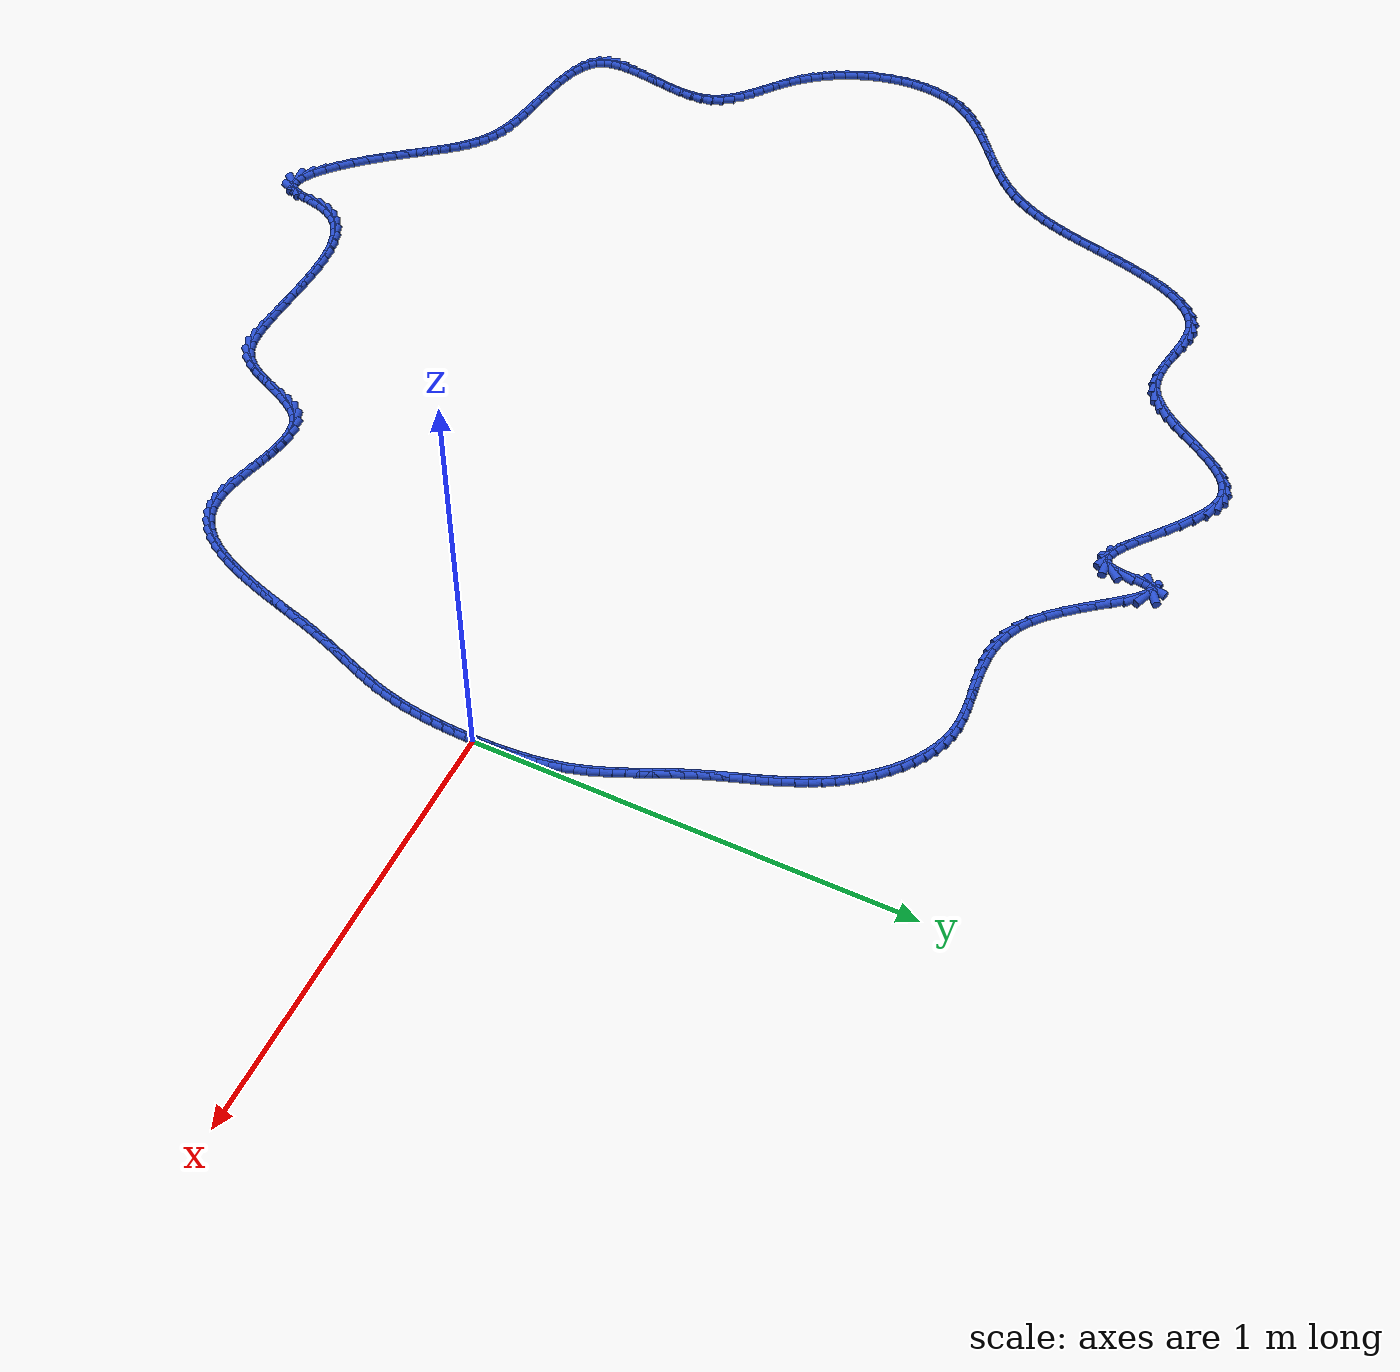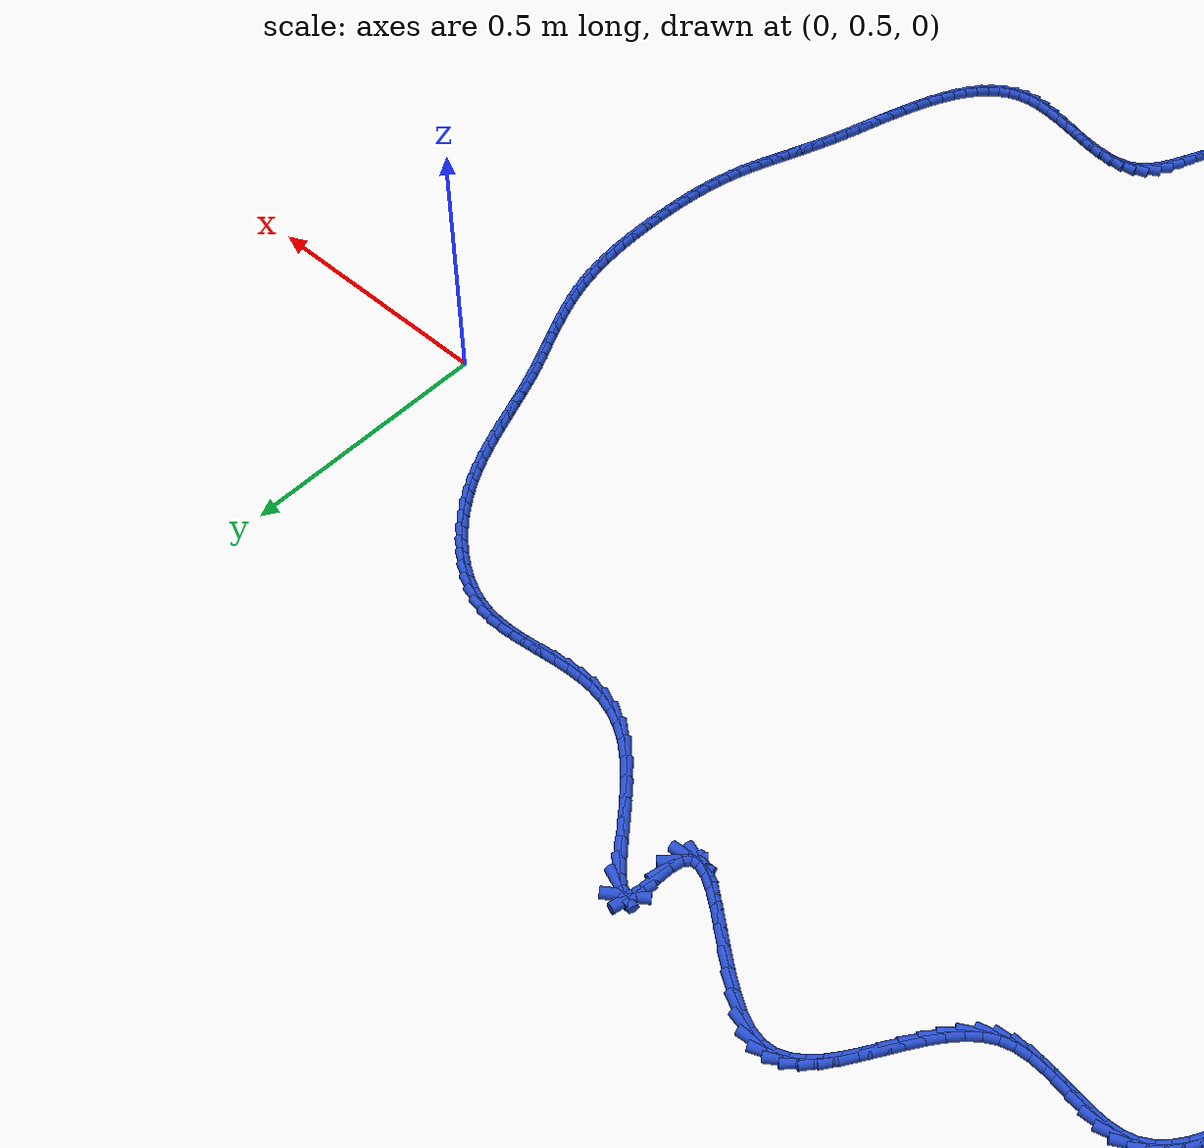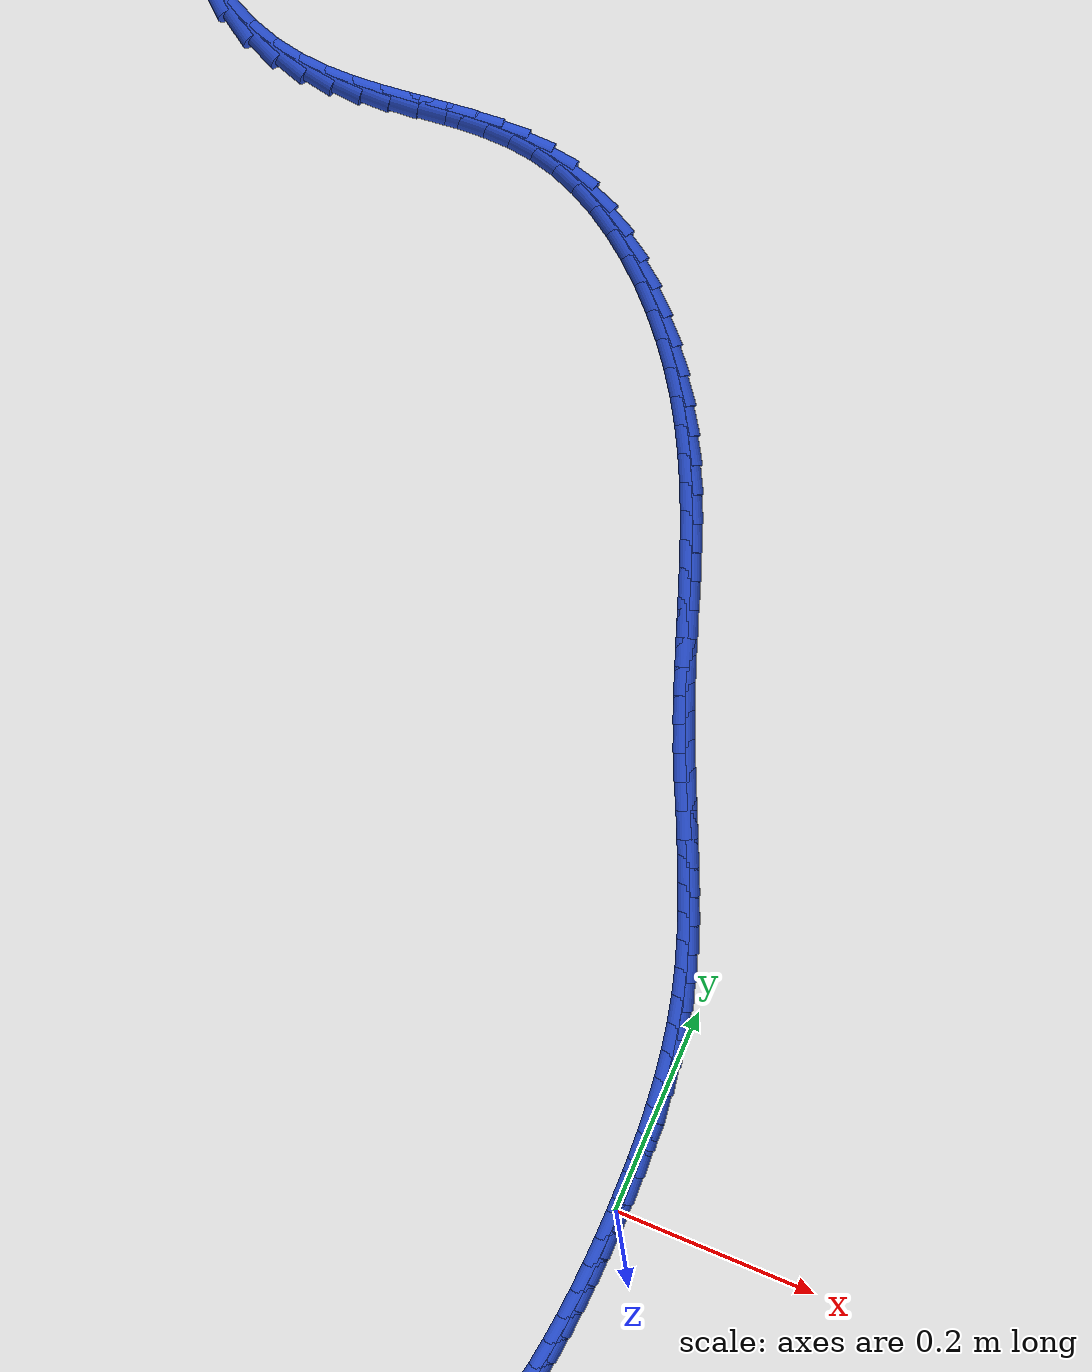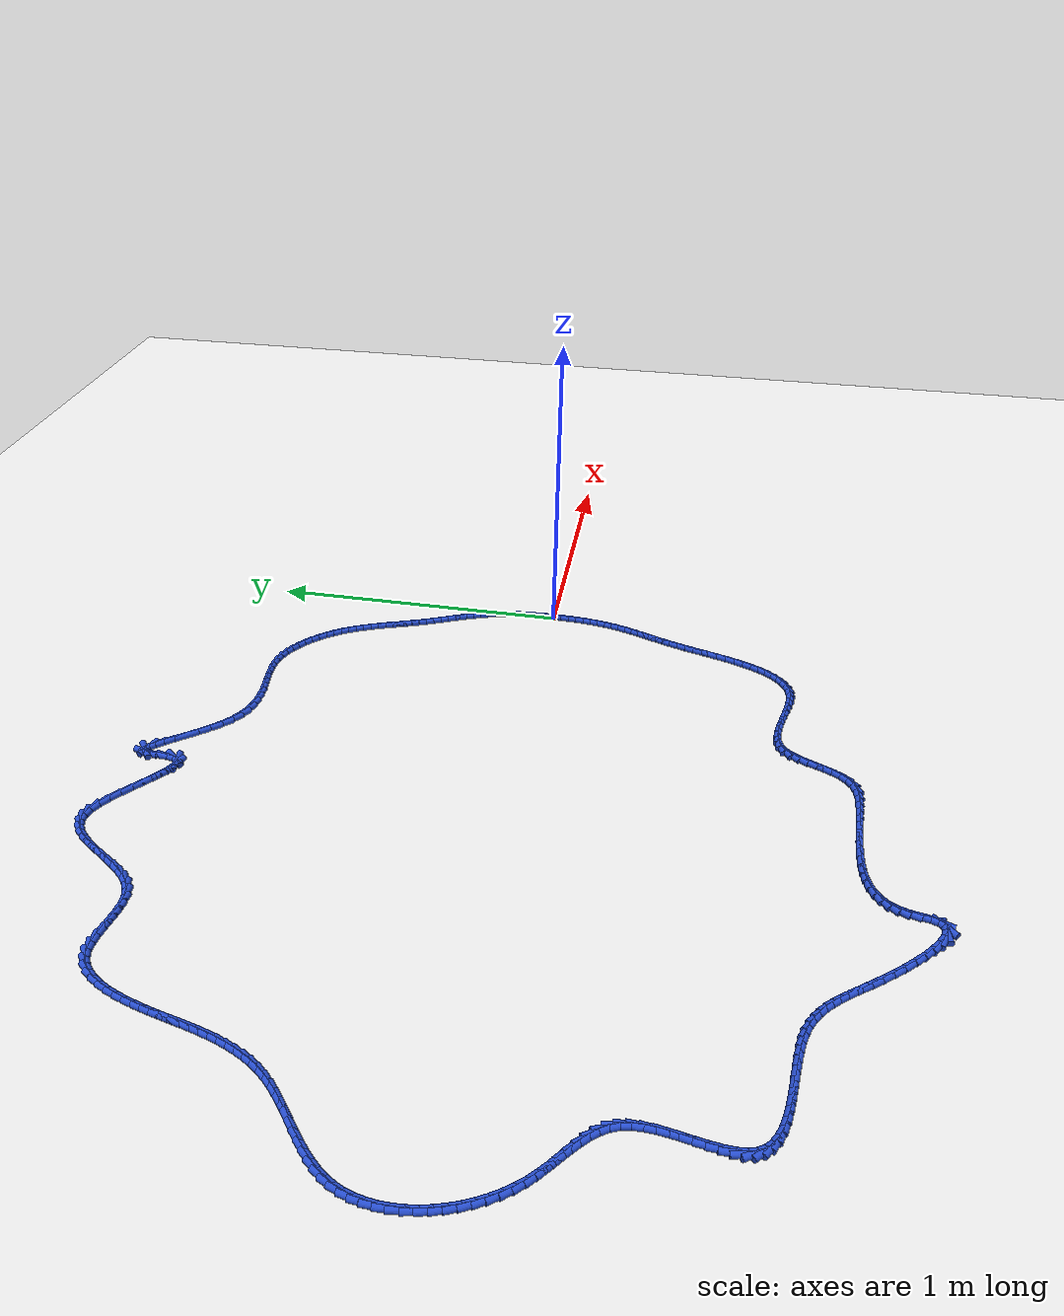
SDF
<sdf version="1.6">
 <world name="default">
  <light name="sun" type="directional">
   <pose>0 0 10 0 -0 0</pose>
   <diffuse>0.8 0.8 0.8 1</diffuse>
   <specular>0.2 0.2 0.2 1</specular>
   <attenuation>
    <range>1000</range>
    <constant>0.9</constant>
    <linear>0.01</linear>
    <quadratic>0.001</quadratic>
   </attenuation>
   <direction>-0.5 0.1 -0.9</direction>
  </light>
  <model name="ground_plane">
   <static>1</static>
   <link name="link">
    <collision name="collision">
     <geometry><plane><normal>0 0 1</normal><size>100 100</size></plane></geometry>
     <surface><friction><ode><mu>100</mu><mu2>50</mu2></ode></friction></surface>
    </collision>
    <visual name="visual">
     <cast_shadows>0</cast_shadows>
     <geometry><plane><normal>0 0 1</normal><size>100 100</size></plane></geometry>
     <material>
      <script><uri>file://media/materials/scripts/gazebo.material</uri><name>Gazebo/WhiteGlow</name></script>
     </material>
    </visual>
   </link>
  </model>
  <gravity>0 0 -9.8</gravity>
  <magnetic_field>6e-06 2.3e-05 -4.2e-05</magnetic_field>
  <atmosphere type="adiabatic"/>
  <physics name="default_physics" default="0" type="ode">
   <max_step_size>0.001</max_step_size>
   <real_time_factor>1</real_time_factor>
   <real_time_update_rate>1000</real_time_update_rate>
  </physics>
  <scene><ambient>0.4 0.4 0.4 1</ambient><background>0.7 0.7 0.7 1</background><shadows>1</shadows></scene>
  <spherical_coordinates>
   <surface_model>EARTH_WGS84</surface_model>
   <latitude_deg>0</latitude_deg>
   <longitude_deg>0</longitude_deg>
   <elevation>0</elevation>
   <heading_deg>0</heading_deg>
  </spherical_coordinates>
  <model name="line">
   <link name="link_0">
    <pose>6.505213034913027e-19 -5.551115123125783e-17 0.01 0 1.57 -1.5686087319512148</pose>
    <collision name="collision">
     <geometry><cylinder><radius>0.01</radius><length>0.08</length></cylinder></geometry>
    </collision>
    <visual name="visual">
     <material>
      <script><name>Gazebo/Blue</name><uri>file://media/materials/scripts/gazebo.material</uri></script>
     </material>
     <geometry><cylinder><radius>0.01</radius><length>0.08</length></cylinder></geometry>
    </visual>
   </link>
   <link name="link_1">
    <pose>-5.87740264083111e-05 0.026866918626301892 0.01 0 1.57 -1.547128762032059</pose>
    <collision name="collision">
     <geometry><cylinder><radius>0.01</radius><length>0.08</length></cylinder></geometry>
    </collision>
    <visual name="visual">
     <material>
      <script><name>Gazebo/Blue</name><uri>file://media/materials/scripts/gazebo.material</uri></script>
     </material>
     <geometry><cylinder><radius>0.01</radius><length>0.08</length></cylinder></geometry>
    </visual>
   </link>
   <link name="link_2">
    <pose>-0.0006926571728951053 0.05364469619251644 0.01 0 1.57 -1.5219949270998772</pose>
    <collision name="collision">
     <geometry><cylinder><radius>0.01</radius><length>0.08</length></cylinder></geometry>
    </collision>
    <visual name="visual">
     <material>
      <script><name>Gazebo/Blue</name><uri>file://media/materials/scripts/gazebo.material</uri></script>
     </material>
     <geometry><cylinder><radius>0.01</radius><length>0.08</length></cylinder></geometry>
    </visual>
   </link>
   <link name="link_3">
    <pose>-0.0019944166031671848 0.08029815000768363 0.01 0 1.57 -1.4931086927876336</pose>
    <collision name="collision">
     <geometry><cylinder><radius>0.01</radius><length>0.08</length></cylinder></geometry>
    </collision>
    <visual name="visual">
     <material>
      <script><name>Gazebo/Blue</name><uri>file://media/materials/scripts/gazebo.material</uri></script>
     </material>
     <geometry><cylinder><radius>0.01</radius><length>0.08</length></cylinder></geometry>
    </visual>
   </link>
   <link name="link_4">
    <pose>-0.00405681948093135 0.10679209738084348 0.01 0 1.57 -1.4603767294404082</pose>
    <collision name="collision">
     <geometry><cylinder><radius>0.01</radius><length>0.08</length></cylinder></geometry>
    </collision>
    <visual name="visual">
     <material>
      <script><name>Gazebo/Blue</name><uri>file://media/materials/scripts/gazebo.material</uri></script>
     </material>
     <geometry><cylinder><radius>0.01</radius><length>0.08</length></cylinder></geometry>
    </visual>
   </link>
   <link name="link_5">
    <pose>-0.006972632969894407 0.13309135562103608 0.01 0 1.57 -1.4237232285010475</pose>
    <collision name="collision">
     <geometry><cylinder><radius>0.01</radius><length>0.08</length></cylinder></geometry>
    </collision>
    <visual name="visual">
     <material>
      <script><name>Gazebo/Blue</name><uri>file://media/materials/scripts/gazebo.material</uri></script>
     </material>
     <geometry><cylinder><radius>0.01</radius><length>0.08</length></cylinder></geometry>
    </visual>
   </link>
   <link name="link_6">
    <pose>-0.010834624233763152 0.1591607420373014 0.01 0 1.57 -1.3831049552878407</pose>
    <collision name="collision">
     <geometry><cylinder><radius>0.01</radius><length>0.08</length></cylinder></geometry>
    </collision>
    <visual name="visual">
     <material>
      <script><name>Gazebo/Blue</name><uri>file://media/materials/scripts/gazebo.material</uri></script>
     </material>
     <geometry><cylinder><radius>0.01</radius><length>0.08</length></cylinder></geometry>
    </visual>
   </link>
   <link name="link_7">
    <pose>-0.015735560436244394 0.18496507393867967 0.01 0 1.57 -1.3385288146965135</pose>
    <collision name="collision">
     <geometry><cylinder><radius>0.01</radius><length>0.08</length></cylinder></geometry>
    </collision>
    <visual name="visual">
     <material>
      <script><name>Gazebo/Blue</name><uri>file://media/materials/scripts/gazebo.material</uri></script>
     </material>
     <geometry><cylinder><radius>0.01</radius><length>0.08</length></cylinder></geometry>
    </visual>
   </link>
   <link name="link_8">
    <pose>-0.02176820874104493 0.2104691686342107 0.01 0 1.57 -1.2903570548218142</pose>
    <collision name="collision">
     <geometry><cylinder><radius>0.01</radius><length>0.08</length></cylinder></geometry>
    </collision>
    <visual name="visual">
     <material>
      <script><name>Gazebo/Blue</name><uri>file://media/materials/scripts/gazebo.material</uri></script>
     </material>
     <geometry><cylinder><radius>0.01</radius><length>0.08</length></cylinder></geometry>
    </visual>
   </link>
   <link name="link_9">
    <pose>-0.02901818906126157 0.23564009117872278 0.01 0 1.57 -1.2446635823595167</pose>
    <collision name="collision">
     <geometry><cylinder><radius>0.01</radius><length>0.08</length></cylinder></geometry>
    </collision>
    <visual name="visual">
     <material>
      <script><name>Gazebo/Blue</name><uri>file://media/materials/scripts/gazebo.material</uri></script>
     </material>
     <geometry><cylinder><radius>0.01</radius><length>0.08</length></cylinder></geometry>
    </visual>
   </link>
   <link name="link_10">
    <pose>-0.03742315385184375 0.26049144105671185 0.01 0 1.57 -1.2071405693610882</pose>
    <collision name="collision">
     <geometry><cylinder><radius>0.01</radius><length>0.08</length></cylinder></geometry>
    </collision>
    <visual name="visual">
     <material>
      <script><name>Gazebo/Blue</name><uri>file://media/materials/scripts/gazebo.material</uri></script>
     </material>
     <geometry><cylinder><radius>0.01</radius><length>0.08</length></cylinder></geometry>
    </visual>
   </link>
   <link name="link_11">
    <pose>-0.04678137299843718 0.28508065231230845 0.01 0 1.57 -1.1779847370844352</pose>
    <collision name="collision">
     <geometry><cylinder><radius>0.01</radius><length>0.08</length></cylinder></geometry>
    </collision>
    <visual name="visual">
     <material>
      <script><name>Gazebo/Blue</name><uri>file://media/materials/scripts/gazebo.material</uri></script>
     </material>
     <geometry><cylinder><radius>0.01</radius><length>0.08</length></cylinder></geometry>
    </visual>
   </link>
   <link name="link_12">
    <pose>-0.056885688036905566 0.30946686615664004 0.01 0 1.57 -1.157097907797772</pose>
    <collision name="collision">
     <geometry><cylinder><radius>0.01</radius><length>0.08</length></cylinder></geometry>
    </collision>
    <visual name="visual">
     <material>
      <script><name>Gazebo/Blue</name><uri>file://media/materials/scripts/gazebo.material</uri></script>
     </material>
     <geometry><cylinder><radius>0.01</radius><length>0.08</length></cylinder></geometry>
    </visual>
   </link>
   <link name="link_13">
    <pose>-0.06752894050311259 0.33370922380083395 0.01 0 1.57 -1.1443649214348135</pose>
    <collision name="collision">
     <geometry><cylinder><radius>0.01</radius><length>0.08</length></cylinder></geometry>
    </collision>
    <visual name="visual">
     <material>
      <script><name>Gazebo/Blue</name><uri>file://media/materials/scripts/gazebo.material</uri></script>
     </material>
     <geometry><cylinder><radius>0.01</radius><length>0.08</length></cylinder></geometry>
    </visual>
   </link>
   <link name="link_14">
    <pose>-0.07850397193292197 0.3578668664560176 0.01 0 1.57 -1.139695200061825</pose>
    <collision name="collision">
     <geometry><cylinder><radius>0.01</radius><length>0.08</length></cylinder></geometry>
    </collision>
    <visual name="visual">
     <material>
      <script><name>Gazebo/Blue</name><uri>file://media/materials/scripts/gazebo.material</uri></script>
     </material>
     <geometry><cylinder><radius>0.01</radius><length>0.08</length></cylinder></geometry>
    </visual>
   </link>
   <link name="link_15">
    <pose>-0.08960362386219746 0.3819989353333187 0.01 0 1.57 -1.1430467912441684</pose>
    <collision name="collision">
     <geometry><cylinder><radius>0.01</radius><length>0.08</length></cylinder></geometry>
    </collision>
    <visual name="visual">
     <material>
      <script><name>Gazebo/Blue</name><uri>file://media/materials/scripts/gazebo.material</uri></script>
     </material>
     <geometry><cylinder><radius>0.01</radius><length>0.08</length></cylinder></geometry>
    </visual>
   </link>
   <link name="link_16">
    <pose>-0.10062073782680275 0.4061645716438645 0.01 0 1.57 -1.1544347715538974</pose>
    <collision name="collision">
     <geometry><cylinder><radius>0.01</radius><length>0.08</length></cylinder></geometry>
    </collision>
    <visual name="visual">
     <material>
      <script><name>Gazebo/Blue</name><uri>file://media/materials/scripts/gazebo.material</uri></script>
     </material>
     <geometry><cylinder><radius>0.01</radius><length>0.08</length></cylinder></geometry>
    </visual>
   </link>
   <link name="link_17">
    <pose>-0.11134815536260154 0.4304229165987823 0.01 0 1.57 -1.1739037138108221</pose>
    <collision name="collision">
     <geometry><cylinder><radius>0.01</radius><length>0.08</length></cylinder></geometry>
    </collision>
    <visual name="visual">
     <material>
      <script><name>Gazebo/Blue</name><uri>file://media/materials/scripts/gazebo.material</uri></script>
     </material>
     <geometry><cylinder><radius>0.01</radius><length>0.08</length></cylinder></geometry>
    </visual>
   </link>
   <link name="link_18">
    <pose>-0.12157925752687783 0.4548329469520125 0.01 0 1.57 -1.1970475792879767</pose>
    <collision name="collision">
     <geometry><cylinder><radius>0.01</radius><length>0.08</length></cylinder></geometry>
    </collision>
    <visual name="visual">
     <material>
      <script><name>Gazebo/Blue</name><uri>file://media/materials/scripts/gazebo.material</uri></script>
     </material>
     <geometry><cylinder><radius>0.01</radius><length>0.08</length></cylinder></geometry>
    </visual>
   </link>
   <link name="link_19">
    <pose>-0.1312214257653941 0.4794188898025247 0.01 0 1.57 -1.2138346116632008</pose>
    <collision name="collision">
     <geometry><cylinder><radius>0.01</radius><length>0.08</length></cylinder></geometry>
    </collision>
    <visual name="visual">
     <material>
      <script><name>Gazebo/Blue</name><uri>file://media/materials/scripts/gazebo.material</uri></script>
     </material>
     <geometry><cylinder><radius>0.01</radius><length>0.08</length></cylinder></geometry>
    </visual>
   </link>
   <link name="link_20">
    <pose>-0.14043620599054032 0.5041274977104818 0.01 0 1.57 -1.2228487040770044</pose>
    <collision name="collision">
     <geometry><cylinder><radius>0.01</radius><length>0.08</length></cylinder></geometry>
    </collision>
    <visual name="visual">
     <material>
      <script><name>Gazebo/Blue</name><uri>file://media/materials/scripts/gazebo.material</uri></script>
     </material>
     <geometry><cylinder><radius>0.01</radius><length>0.08</length></cylinder></geometry>
    </visual>
   </link>
   <link name="link_21">
    <pose>-0.14941950550877955 0.5288950491788588 0.01 0 1.57 -1.2240569381717366</pose>
    <collision name="collision">
     <geometry><cylinder><radius>0.01</radius><length>0.08</length></cylinder></geometry>
    </collision>
    <visual name="visual">
     <material>
      <script><name>Gazebo/Blue</name><uri>file://media/materials/scripts/gazebo.material</uri></script>
     </material>
     <geometry><cylinder><radius>0.01</radius><length>0.08</length></cylinder></geometry>
    </visual>
   </link>
   <link name="link_22">
    <pose>-0.15836723162657484 0.55365782271063 0.01 0 1.57 -1.2174433859761682</pose>
    <collision name="collision">
     <geometry><cylinder><radius>0.01</radius><length>0.08</length></cylinder></geometry>
    </collision>
    <visual name="visual">
     <material>
      <script><name>Gazebo/Blue</name><uri>file://media/materials/scripts/gazebo.material</uri></script>
     </material>
     <geometry><cylinder><radius>0.01</radius><length>0.08</length></cylinder></geometry>
    </visual>
   </link>
   <link name="link_23">
    <pose>-0.16747529165038938 0.5783520968087708 0.01 0 1.57 -1.2030070187508424</pose>
    <collision name="collision">
     <geometry><cylinder><radius>0.01</radius><length>0.08</length></cylinder></geometry>
    </collision>
    <visual name="visual">
     <material>
      <script><name>Gazebo/Blue</name><uri>file://media/materials/scripts/gazebo.material</uri></script>
     </material>
     <geometry><cylinder><radius>0.01</radius><length>0.08</length></cylinder></geometry>
    </visual>
   </link>
   <link name="link_24">
    <pose>-0.1769395928866861 0.6029141499762559 0.01 0 1.57 -1.1807738515280444</pose>
    <collision name="collision">
     <geometry><cylinder><radius>0.01</radius><length>0.08</length></cylinder></geometry>
    </collision>
    <visual name="visual">
     <material>
      <script><name>Gazebo/Blue</name><uri>file://media/materials/scripts/gazebo.material</uri></script>
     </material>
     <geometry><cylinder><radius>0.01</radius><length>0.08</length></cylinder></geometry>
    </visual>
   </link>
   <link name="link_25">
    <pose>-0.18695604264192822 0.6272802607160602 0.01 0 1.57 -1.1508230185935548</pose>
    <collision name="collision">
     <geometry><cylinder><radius>0.01</radius><length>0.08</length></cylinder></geometry>
    </collision>
    <visual name="visual">
     <material>
      <script><name>Gazebo/Blue</name><uri>file://media/materials/scripts/gazebo.material</uri></script>
     </material>
     <geometry><cylinder><radius>0.01</radius><length>0.08</length></cylinder></geometry>
    </visual>
   </link>
   <link name="link_26">
    <pose>-0.1977205482225787 0.6513867075311587 0.01 0 1.57 -1.113325383090786</pose>
    <collision name="collision">
     <geometry><cylinder><radius>0.01</radius><length>0.08</length></cylinder></geometry>
    </collision>
    <visual name="visual">
     <material>
      <script><name>Gazebo/Blue</name><uri>file://media/materials/scripts/gazebo.material</uri></script>
     </material>
     <geometry><cylinder><radius>0.01</radius><length>0.08</length></cylinder></geometry>
    </visual>
   </link>
   <link name="link_27">
    <pose>-0.20942901693510063 0.6751697689245258 0.01 0 1.57 -1.068591139055498</pose>
    <collision name="collision">
     <geometry><cylinder><radius>0.01</radius><length>0.08</length></cylinder></geometry>
    </collision>
    <visual name="visual">
     <material>
      <script><name>Gazebo/Blue</name><uri>file://media/materials/scripts/gazebo.material</uri></script>
     </material>
     <geometry><cylinder><radius>0.01</radius><length>0.08</length></cylinder></geometry>
    </visual>
   </link>
   <link name="link_28">
    <pose>-0.22227735608595725 0.6985657233991371 0.01 0 1.57 -1.0171195089741287</pose>
    <collision name="collision">
     <geometry><cylinder><radius>0.01</radius><length>0.08</length></cylinder></geometry>
    </collision>
    <visual name="visual">
     <material>
      <script><name>Gazebo/Blue</name><uri>file://media/materials/scripts/gazebo.material</uri></script>
     </material>
     <geometry><cylinder><radius>0.01</radius><length>0.08</length></cylinder></geometry>
    </visual>
   </link>
   <link name="link_29">
    <pose>-0.2364614729816115 0.721510849457967 0.01 0 1.57 -0.9597408084259309</pose>
    <collision name="collision">
     <geometry><cylinder><radius>0.01</radius><length>0.08</length></cylinder></geometry>
    </collision>
    <visual name="visual">
     <material>
      <script><name>Gazebo/Blue</name><uri>file://media/materials/scripts/gazebo.material</uri></script>
     </material>
     <geometry><cylinder><radius>0.01</radius><length>0.08</length></cylinder></geometry>
    </visual>
   </link>
   <link name="link_30">
    <pose>-0.25217080556211285 0.7439370180234688 0.01 0 1.57 -0.899408453424222</pose>
    <collision name="collision">
     <geometry><cylinder><radius>0.01</radius><length>0.08</length></cylinder></geometry>
    </collision>
    <visual name="visual">
     <material>
      <script><name>Gazebo/Blue</name><uri>file://media/materials/scripts/gazebo.material</uri></script>
     </material>
     <geometry><cylinder><radius>0.01</radius><length>0.08</length></cylinder></geometry>
    </visual>
   </link>
   <link name="link_31">
    <pose>-0.2694367490758823 0.7656684255033538 0.01 0 1.57 -0.8375553751071845</pose>
    <collision name="collision">
     <geometry><cylinder><radius>0.01</radius><length>0.08</length></cylinder></geometry>
    </collision>
    <visual name="visual">
     <material>
      <script><name>Gazebo/Blue</name><uri>file://media/materials/scripts/gazebo.material</uri></script>
     </material>
     <geometry><cylinder><radius>0.01</radius><length>0.08</length></cylinder></geometry>
    </visual>
   </link>
   <link name="link_32">
    <pose>-0.28812734133071144 0.7864179728511262 0.01 0 1.57 -0.77271760801657</pose>
    <collision name="collision">
     <geometry><cylinder><radius>0.01</radius><length>0.08</length></cylinder></geometry>
    </collision>
    <visual name="visual">
     <material>
      <script><name>Gazebo/Blue</name><uri>file://media/materials/scripts/gazebo.material</uri></script>
     </material>
     <geometry><cylinder><radius>0.01</radius><length>0.08</length></cylinder></geometry>
    </visual>
   </link>
   <link name="link_33">
    <pose>-0.3081030874536311 0.805893429003508 0.01 0 1.57 -0.7032817532625969</pose>
    <collision name="collision">
     <geometry><cylinder><radius>0.01</radius><length>0.08</length></cylinder></geometry>
    </collision>
    <visual name="visual">
     <material>
      <script><name>Gazebo/Blue</name><uri>file://media/materials/scripts/gazebo.material</uri></script>
     </material>
     <geometry><cylinder><radius>0.01</radius><length>0.08</length></cylinder></geometry>
    </visual>
   </link>
   <link name="link_34">
    <pose>-0.3292244925716726 0.8238025628972219 0.01 0 1.57 -0.6275478799582125</pose>
    <collision name="collision">
     <geometry><cylinder><radius>0.01</radius><length>0.08</length></cylinder></geometry>
    </collision>
    <visual name="visual">
     <material>
      <script><name>Gazebo/Blue</name><uri>file://media/materials/scripts/gazebo.material</uri></script>
     </material>
     <geometry><cylinder><radius>0.01</radius><length>0.08</length></cylinder></geometry>
    </visual>
   </link>
   <link name="link_35">
    <pose>-0.35135206181186673 0.83985314346899 0.01 0 1.57 -0.5437147174878636</pose>
    <collision name="collision">
     <geometry><cylinder><radius>0.01</radius><length>0.08</length></cylinder></geometry>
    </collision>
    <visual name="visual">
     <material>
      <script><name>Gazebo/Blue</name><uri>file://media/materials/scripts/gazebo.material</uri></script>
     </material>
     <geometry><cylinder><radius>0.01</radius><length>0.08</length></cylinder></geometry>
    </visual>
   </link>
   <link name="link_36">
    <pose>-0.3743463003012447 0.8537529396555349 0.01 0 1.57 -0.4499327340533218</pose>
    <collision name="collision">
     <geometry><cylinder><radius>0.01</radius><length>0.08</length></cylinder></geometry>
    </collision>
    <visual name="visual">
     <material>
      <script><name>Gazebo/Blue</name><uri>file://media/materials/scripts/gazebo.material</uri></script>
     </material>
     <geometry><cylinder><radius>0.01</radius><length>0.08</length></cylinder></geometry>
    </visual>
   </link>
   <link name="link_37">
    <pose>-0.39806771316683776 0.8652097203935789 0.01 0 1.57 -0.34447214646214636</pose>
    <collision name="collision">
     <geometry><cylinder><radius>0.01</radius><length>0.08</length></cylinder></geometry>
    </collision>
    <visual name="visual">
     <material>
      <script><name>Gazebo/Blue</name><uri>file://media/materials/scripts/gazebo.material</uri></script>
     </material>
     <geometry><cylinder><radius>0.01</radius><length>0.08</length></cylinder></geometry>
    </visual>
   </link>
   <link name="link_38">
    <pose>-0.4223768055356765 0.8739312546198446 0.01 0 1.57 -0.22607082859793198</pose>
    <collision name="collision">
     <geometry><cylinder><radius>0.01</radius><length>0.08</length></cylinder></geometry>
    </collision>
    <visual name="visual">
     <material>
      <script><name>Gazebo/Blue</name><uri>file://media/materials/scripts/gazebo.material</uri></script>
     </material>
     <geometry><cylinder><radius>0.01</radius><length>0.08</length></cylinder></geometry>
    </visual>
   </link>
   <link name="link_39">
    <pose>-0.4471341040816441 0.87962549690458 0.01 0 1.57 -0.10298715858292842</pose>
    <collision name="collision">
     <geometry><cylinder><radius>0.01</radius><length>0.08</length></cylinder></geometry>
    </collision>
    <visual name="visual">
     <material>
      <script><name>Gazebo/Blue</name><uri>file://media/materials/scripts/gazebo.material</uri></script>
     </material>
     <geometry><cylinder><radius>0.01</radius><length>0.08</length></cylinder></geometry>
    </visual>
   </link>
   <link name="link_40">
    <pose>-0.47222548090375766 0.8822187613588304 0.01 0 1.57 -0.002320954017408585</pose>
    <collision name="collision">
     <geometry><cylinder><radius>0.01</radius><length>0.08</length></cylinder></geometry>
    </collision>
    <visual name="visual">
     <material>
      <script><name>Gazebo/Blue</name><uri>file://media/materials/scripts/gazebo.material</uri></script>
     </material>
     <geometry><cylinder><radius>0.01</radius><length>0.08</length></cylinder></geometry>
    </visual>
   </link>
   <link name="link_41">
    <pose>-0.4976111311162816 0.8822776803914713 0.01 0 1.57 0.06974142340890807</pose>
    <collision name="collision">
     <geometry><cylinder><radius>0.01</radius><length>0.08</length></cylinder></geometry>
    </collision>
    <visual name="visual">
     <material>
      <script><name>Gazebo/Blue</name><uri>file://media/materials/scripts/gazebo.material</uri></script>
     </material>
     <geometry><cylinder><radius>0.01</radius><length>0.08</length></cylinder></geometry>
    </visual>
   </link>
   <link name="link_42">
    <pose>-0.5232648028691199 0.8804856504673396 0.01 0 1.57 0.11379594841330783</pose>
    <collision name="collision">
     <geometry><cylinder><radius>0.01</radius><length>0.08</length></cylinder></geometry>
    </collision>
    <visual name="visual">
     <material>
      <script><name>Gazebo/Blue</name><uri>file://media/materials/scripts/gazebo.material</uri></script>
     </material>
     <geometry><cylinder><radius>0.01</radius><length>0.08</length></cylinder></geometry>
    </visual>
   </link>
   <link name="link_43">
    <pose>-0.5491602443121776 0.8775260680512726 0.01 0 1.57 0.13113178850228505</pose>
    <collision name="collision">
     <geometry><cylinder><radius>0.01</radius><length>0.08</length></cylinder></geometry>
    </collision>
    <visual name="visual">
     <material>
      <script><name>Gazebo/Blue</name><uri>file://media/materials/scripts/gazebo.material</uri></script>
     </material>
     <geometry><cylinder><radius>0.01</radius><length>0.08</length></cylinder></geometry>
    </visual>
   </link>
   <link name="link_44">
    <pose>-0.5752712035953587 0.8740823296081065 0.01 0 1.57 0.12274372895697669</pose>
    <collision name="collision">
     <geometry><cylinder><radius>0.01</radius><length>0.08</length></cylinder></geometry>
    </collision>
    <visual name="visual">
     <material>
      <script><name>Gazebo/Blue</name><uri>file://media/materials/scripts/gazebo.material</uri></script>
     </material>
     <geometry><cylinder><radius>0.01</radius><length>0.08</length></cylinder></geometry>
    </visual>
   </link>
   <link name="link_45">
    <pose>-0.6015714288685676 0.8708378316026787 0.01 0 1.57 0.0890147874672357</pose>
    <collision name="collision">
     <geometry><cylinder><radius>0.01</radius><length>0.08</length></cylinder></geometry>
    </collision>
    <visual name="visual">
     <material>
      <script><name>Gazebo/Blue</name><uri>file://media/materials/scripts/gazebo.material</uri></script>
     </material>
     <geometry><cylinder><radius>0.01</radius><length>0.08</length></cylinder></geometry>
    </visual>
   </link>
   <link name="link_46">
    <pose>-0.628034668281709 0.8684759704998253 0.01 0 1.57 0.029909412094079497</pose>
    <collision name="collision">
     <geometry><cylinder><radius>0.01</radius><length>0.08</length></cylinder></geometry>
    </collision>
    <visual name="visual">
     <material>
      <script><name>Gazebo/Blue</name><uri>file://media/materials/scripts/gazebo.material</uri></script>
     </material>
     <geometry><cylinder><radius>0.01</radius><length>0.08</length></cylinder></geometry>
    </visual>
   </link>
   <link name="link_47">
    <pose>-0.654634669984687 0.8676801427643837 0.01 0 1.57 -0.054366971205347565</pose>
    <collision name="collision">
     <geometry><cylinder><radius>0.01</radius><length>0.08</length></cylinder></geometry>
    </collision>
    <visual name="visual">
     <material>
      <script><name>Gazebo/Blue</name><uri>file://media/materials/scripts/gazebo.material</uri></script>
     </material>
     <geometry><cylinder><radius>0.01</radius><length>0.08</length></cylinder></geometry>
    </visual>
   </link>
   <link name="link_48">
    <pose>-0.6813451821274064 0.8691337448611905 0.01 0 1.57 -0.16226533208964797</pose>
    <collision name="collision">
     <geometry><cylinder><radius>0.01</radius><length>0.08</length></cylinder></geometry>
    </collision>
    <visual name="visual">
     <material>
      <script><name>Gazebo/Blue</name><uri>file://media/materials/scripts/gazebo.material</uri></script>
     </material>
     <geometry><cylinder><radius>0.01</radius><length>0.08</length></cylinder></geometry>
    </visual>
   </link>
   <link name="link_49">
    <pose>-0.7081399528597709 0.8735201732550825 0.01 0 1.57 -0.28963882757512166</pose>
    <collision name="collision">
     <geometry><cylinder><radius>0.01</radius><length>0.08</length></cylinder></geometry>
    </collision>
    <visual name="visual">
     <material>
      <script><name>Gazebo/Blue</name><uri>file://media/materials/scripts/gazebo.material</uri></script>
     </material>
     <geometry><cylinder><radius>0.01</radius><length>0.08</length></cylinder></geometry>
    </visual>
   </link>
   <link name="link_50">
    <pose>-0.7349927303316856 0.8815228244108965 0.01 0 1.57 -0.42915326692551714</pose>
    <collision name="collision">
     <geometry><cylinder><radius>0.01</radius><length>0.08</length></cylinder></geometry>
    </collision>
    <visual name="visual">
     <material>
      <script><name>Gazebo/Blue</name><uri>file://media/materials/scripts/gazebo.material</uri></script>
     </material>
     <geometry><cylinder><radius>0.01</radius><length>0.08</length></cylinder></geometry>
    </visual>
   </link>
   <link name="link_51">
    <pose>-0.7618772626930542 0.8938250947934692 0.01 0 1.57 -0.5713068168496578</pose>
    <collision name="collision">
     <geometry><cylinder><radius>0.01</radius><length>0.08</length></cylinder></geometry>
    </collision>
    <visual name="visual">
     <material>
      <script><name>Gazebo/Blue</name><uri>file://media/materials/scripts/gazebo.material</uri></script>
     </material>
     <geometry><cylinder><radius>0.01</radius><length>0.08</length></cylinder></geometry>
    </visual>
   </link>
   <link name="link_52">
    <pose>-0.7887672980937819 0.9111103808676373 0.01 0 1.57 -0.702711851077366</pose>
    <collision name="collision">
     <geometry><cylinder><radius>0.01</radius><length>0.08</length></cylinder></geometry>
    </collision>
    <visual name="visual">
     <material>
      <script><name>Gazebo/Blue</name><uri>file://media/materials/scripts/gazebo.material</uri></script>
     </material>
     <geometry><cylinder><radius>0.01</radius><length>0.08</length></cylinder></geometry>
    </visual>
   </link>
   <link name="link_53">
    <pose>-0.8156023096300639 0.9338378854064251 0.01 0 1.57 -0.7954593921653529</pose>
    <collision name="collision">
     <geometry><cylinder><radius>0.01</radius><length>0.08</length></cylinder></geometry>
    </collision>
    <visual name="visual">
     <material>
      <script><name>Gazebo/Blue</name><uri>file://media/materials/scripts/gazebo.material</uri></script>
     </material>
     <geometry><cylinder><radius>0.01</radius><length>0.08</length></cylinder></geometry>
    </visual>
   </link>
   <link name="link_54">
    <pose>-0.8420742794039541 0.96084796850682 0.01 0 1.57 -0.8529702942589156</pose>
    <collision name="collision">
     <geometry><cylinder><radius>0.01</radius><length>0.08</length></cylinder></geometry>
    </collision>
    <visual name="visual">
     <material>
      <script><name>Gazebo/Blue</name><uri>file://media/materials/scripts/gazebo.material</uri></script>
     </material>
     <geometry><cylinder><radius>0.01</radius><length>0.08</length></cylinder></geometry>
    </visual>
   </link>
   <link name="link_55">
    <pose>-0.8677665016303032 0.9902700610023644 0.01 0 1.57 -0.885423175201356</pose>
    <collision name="collision">
     <geometry><cylinder><radius>0.01</radius><length>0.08</length></cylinder></geometry>
    </collision>
    <visual name="visual">
     <material>
      <script><name>Gazebo/Blue</name><uri>file://media/materials/scripts/gazebo.material</uri></script>
     </material>
     <geometry><cylinder><radius>0.01</radius><length>0.08</length></cylinder></geometry>
    </visual>
   </link>
   <link name="link_56">
    <pose>-0.8922618040260977 1.0202305423563838 0.01 0 1.57 -0.8964600163468273</pose>
    <collision name="collision">
     <geometry><cylinder><radius>0.01</radius><length>0.08</length></cylinder></geometry>
    </collision>
    <visual name="visual">
     <material>
      <script><name>Gazebo/Blue</name><uri>file://media/materials/scripts/gazebo.material</uri></script>
     </material>
     <geometry><cylinder><radius>0.01</radius><length>0.08</length></cylinder></geometry>
    </visual>
   </link>
   <link name="link_57">
    <pose>-0.9151430143083257 1.048855792032206 0.01 0 1.57 -0.8837787406177134</pose>
    <collision name="collision">
     <geometry><cylinder><radius>0.01</radius><length>0.08</length></cylinder></geometry>
    </collision>
    <visual name="visual">
     <material>
      <script><name>Gazebo/Blue</name><uri>file://media/materials/scripts/gazebo.material</uri></script>
     </material>
     <geometry><cylinder><radius>0.01</radius><length>0.08</length></cylinder></geometry>
    </visual>
   </link>
   <link name="link_58">
    <pose>-0.9359929601939737 1.0742721894931553 0.01 0 1.57 -0.8352443787971953</pose>
    <collision name="collision">
     <geometry><cylinder><radius>0.01</radius><length>0.08</length></cylinder></geometry>
    </collision>
    <visual name="visual">
     <material>
      <script><name>Gazebo/Blue</name><uri>file://media/materials/scripts/gazebo.material</uri></script>
     </material>
     <geometry><cylinder><radius>0.01</radius><length>0.08</length></cylinder></geometry>
    </visual>
   </link>
   <link name="link_59">
    <pose>-0.9543944694000296 1.0946061142025592 0.01 0 1.57 -0.7108981038551088</pose>
    <collision name="collision">
     <geometry><cylinder><radius>0.01</radius><length>0.08</length></cylinder></geometry>
    </collision>
    <visual name="visual">
     <material>
      <script><name>Gazebo/Blue</name><uri>file://media/materials/scripts/gazebo.material</uri></script>
     </material>
     <geometry><cylinder><radius>0.01</radius><length>0.08</length></cylinder></geometry>
    </visual>
   </link>
   <link name="link_60">
    <pose>-0.9699303696434805 1.107983945623744 0.01 0 1.57 -0.3554177809435994</pose>
    <collision name="collision">
     <geometry><cylinder><radius>0.01</radius><length>0.08</length></cylinder></geometry>
    </collision>
    <visual name="visual">
     <material>
      <script><name>Gazebo/Blue</name><uri>file://media/materials/scripts/gazebo.material</uri></script>
     </material>
     <geometry><cylinder><radius>0.01</radius><length>0.08</length></cylinder></geometry>
    </visual>
   </link>
   <link name="link_61">
    <pose>-0.9821834886413139 1.1125320632200357 0.01 0 1.57 0.6237872123146154</pose>
    <collision name="collision">
     <geometry><cylinder><radius>0.01</radius><length>0.08</length></cylinder></geometry>
    </collision>
    <visual name="visual">
     <material>
      <script><name>Gazebo/Blue</name><uri>file://media/materials/scripts/gazebo.material</uri></script>
     </material>
     <geometry><cylinder><radius>0.01</radius><length>0.08</length></cylinder></geometry>
    </visual>
   </link>
   <link name="link_62">
    <pose>-0.9907366541105165 1.1063768464547605 0.01 0 1.57 1.3309585675446347</pose>
    <collision name="collision">
     <geometry><cylinder><radius>0.01</radius><length>0.08</length></cylinder></geometry>
    </collision>
    <visual name="visual">
     <material>
      <script><name>Gazebo/Blue</name><uri>file://media/materials/scripts/gazebo.material</uri></script>
     </material>
     <geometry><cylinder><radius>0.01</radius><length>0.08</length></cylinder></geometry>
    </visual>
   </link>
   <link name="link_63">
    <pose>-0.9952581744897983 1.0878873048573479 0.01 0 1.57 1.5032697886254116</pose>
    <collision name="collision">
     <geometry><cylinder><radius>0.01</radius><length>0.08</length></cylinder></geometry>
    </collision>
    <visual name="visual">
     <material>
      <script><name>Gazebo/Blue</name><uri>file://media/materials/scripts/gazebo.material</uri></script>
     </material>
     <geometry><cylinder><radius>0.01</radius><length>0.08</length></cylinder></geometry>
    </visual>
   </link>
   <link name="link_64">
    <pose>-0.9971250705925138 1.0602824888560398 0.01 0 1.57 1.4963026147878422</pose>
    <collision name="collision">
     <geometry><cylinder><radius>0.01</radius><length>0.08</length></cylinder></geometry>
    </collision>
    <visual name="visual">
     <material>
      <script><name>Gazebo/Blue</name><uri>file://media/materials/scripts/gazebo.material</uri></script>
     </material>
     <geometry><cylinder><radius>0.01</radius><length>0.08</length></cylinder></geometry>
    </visual>
   </link>
   <link name="link_65">
    <pose>-0.9992912682402216 1.0312573653041073 0.01 0 1.57 1.333687186073003</pose>
    <collision name="collision">
     <geometry><cylinder><radius>0.01</radius><length>0.08</length></cylinder></geometry>
    </collision>
    <visual name="visual">
     <material>
      <script><name>Gazebo/Blue</name><uri>file://media/materials/scripts/gazebo.material</uri></script>
     </material>
     <geometry><cylinder><radius>0.01</radius><length>0.08</length></cylinder></geometry>
    </visual>
   </link>
   <link name="link_66">
    <pose>-1.004756712619229 1.0086406301502508 0.01 0 1.57 0.8314963425214267</pose>
    <collision name="collision">
     <geometry><cylinder><radius>0.01</radius><length>0.08</length></cylinder></geometry>
    </collision>
    <visual name="visual">
     <material>
      <script><name>Gazebo/Blue</name><uri>file://media/materials/scripts/gazebo.material</uri></script>
     </material>
     <geometry><cylinder><radius>0.01</radius><length>0.08</length></cylinder></geometry>
    </visual>
   </link>
   <link name="link_67">
    <pose>-1.0152979522855266 0.9970798031304884 0.01 0 1.57 0.10446281226366583</pose>
    <collision name="collision">
     <geometry><cylinder><radius>0.01</radius><length>0.08</length></cylinder></geometry>
    </collision>
    <visual name="visual">
     <material>
      <script><name>Gazebo/Blue</name><uri>file://media/materials/scripts/gazebo.material</uri></script>
     </material>
     <geometry><cylinder><radius>0.01</radius><length>0.08</length></cylinder></geometry>
    </visual>
   </link>
   <link name="link_68">
    <pose>-1.0304860116292343 0.9954874192350028 0.01 0 1.57 -0.3355795880335293</pose>
    <collision name="collision">
     <geometry><cylinder><radius>0.01</radius><length>0.08</length></cylinder></geometry>
    </collision>
    <visual name="visual">
     <material>
      <script><name>Gazebo/Blue</name><uri>file://media/materials/scripts/gazebo.material</uri></script>
     </material>
     <geometry><cylinder><radius>0.01</radius><length>0.08</length></cylinder></geometry>
    </visual>
   </link>
   <link name="link_69">
    <pose>-1.0496607918181413 1.0021750279037025 0.01 0 1.57 -0.5331436619504716</pose>
    <collision name="collision">
     <geometry><cylinder><radius>0.01</radius><length>0.08</length></cylinder></geometry>
    </collision>
    <visual name="visual">
     <material>
      <script><name>Gazebo/Blue</name><uri>file://media/materials/scripts/gazebo.material</uri></script>
     </material>
     <geometry><cylinder><radius>0.01</radius><length>0.08</length></cylinder></geometry>
    </visual>
   </link>
   <link name="link_70">
    <pose>-1.0721621940200374 1.0154541785764952 0.01 0 1.57 -0.6256262199374254</pose>
    <collision name="collision">
     <geometry><cylinder><radius>0.01</radius><length>0.08</length></cylinder></geometry>
    </collision>
    <visual name="visual">
     <material>
      <script><name>Gazebo/Blue</name><uri>file://media/materials/scripts/gazebo.material</uri></script>
     </material>
     <geometry><cylinder><radius>0.01</radius><length>0.08</length></cylinder></geometry>
    </visual>
   </link>
   <link name="link_71">
    <pose>-1.0973301194027114 1.0336364206932893 0.01 0 1.57 -0.6670061128003449</pose>
    <collision name="collision">
     <geometry><cylinder><radius>0.01</radius><length>0.08</length></cylinder></geometry>
    </collision>
    <visual name="visual">
     <material>
      <script><name>Gazebo/Blue</name><uri>file://media/materials/scripts/gazebo.material</uri></script>
     </material>
     <geometry><cylinder><radius>0.01</radius><length>0.08</length></cylinder></geometry>
    </visual>
   </link>
   <link name="link_72">
    <pose>-1.1245044691339532 1.0550333036939925 0.01 0 1.57 -0.6770144145226347</pose>
    <collision name="collision">
     <geometry><cylinder><radius>0.01</radius><length>0.08</length></cylinder></geometry>
    </collision>
    <visual name="visual">
     <material>
      <script><name>Gazebo/Blue</name><uri>file://media/materials/scripts/gazebo.material</uri></script>
     </material>
     <geometry><cylinder><radius>0.01</radius><length>0.08</length></cylinder></geometry>
    </visual>
   </link>
   <link name="link_73">
    <pose>-1.1530251443815525 1.077956377018514 0.01 0 1.57 -0.6619882557165395</pose>
    <collision name="collision">
     <geometry><cylinder><radius>0.01</radius><length>0.08</length></cylinder></geometry>
    </collision>
    <visual name="visual">
     <material>
      <script><name>Gazebo/Blue</name><uri>file://media/materials/scripts/gazebo.material</uri></script>
     </material>
     <geometry><cylinder><radius>0.01</radius><length>0.08</length></cylinder></geometry>
    </visual>
   </link>
   <link name="link_74">
    <pose>-1.1822320463132976 1.1007171901067612 0.01 0 1.57 -0.620914360654276</pose>
    <collision name="collision">
     <geometry><cylinder><radius>0.01</radius><length>0.08</length></cylinder></geometry>
    </collision>
    <visual name="visual">
     <material>
      <script><name>Gazebo/Blue</name><uri>file://media/materials/scripts/gazebo.material</uri></script>
     </material>
     <geometry><cylinder><radius>0.01</radius><length>0.08</length></cylinder></geometry>
    </visual>
   </link>
   <link name="link_75">
    <pose>-1.2114650760969794 1.1216272923986423 0.01 0 1.57 -0.5458396638599382</pose>
    <collision name="collision">
     <geometry><cylinder><radius>0.01</radius><length>0.08</length></cylinder></geometry>
    </collision>
    <visual name="visual">
     <material>
      <script><name>Gazebo/Blue</name><uri>file://media/materials/scripts/gazebo.material</uri></script>
     </material>
     <geometry><cylinder><radius>0.01</radius><length>0.08</length></cylinder></geometry>
    </visual>
   </link>
   <link name="link_76">
    <pose>-1.240064134900386 1.1389982333340656 0.01 0 1.57 -0.41846218507310134</pose>
    <collision name="collision">
     <geometry><cylinder><radius>0.01</radius><length>0.08</length></cylinder></geometry>
    </collision>
    <visual name="visual">
     <material>
      <script><name>Gazebo/Blue</name><uri>file://media/materials/scripts/gazebo.material</uri></script>
     </material>
     <geometry><cylinder><radius>0.01</radius><length>0.08</length></cylinder></geometry>
    </visual>
   </link>
   <link name="link_77">
    <pose>-1.2673691238913072 1.1511415623529393 0.01 0 1.57 -0.2042823062850363</pose>
    <collision name="collision">
     <geometry><cylinder><radius>0.01</radius><length>0.08</length></cylinder></geometry>
    </collision>
    <visual name="visual">
     <material>
      <script><name>Gazebo/Blue</name><uri>file://media/materials/scripts/gazebo.material</uri></script>
     </material>
     <geometry><cylinder><radius>0.01</radius><length>0.08</length></cylinder></geometry>
    </visual>
   </link>
   <link name="link_78">
    <pose>-1.2927297216450682 1.1563955733937752 0.01 0 1.57 0.09427145604456666</pose>
    <collision name="collision">
     <geometry><cylinder><radius>0.01</radius><length>0.08</length></cylinder></geometry>
    </collision>
    <visual name="visual">
     <material>
      <script><name>Gazebo/Blue</name><uri>file://media/materials/scripts/gazebo.material</uri></script>
     </material>
     <geometry><cylinder><radius>0.01</radius><length>0.08</length></cylinder></geometry>
    </visual>
   </link>
   <link name="link_79">
    <pose>-1.315900025350138 1.1542047813433638 0.01 0 1.57 0.38877565157395133</pose>
    <collision name="collision">
     <geometry><cylinder><radius>0.01</radius><length>0.08</length></cylinder></geometry>
    </collision>
    <visual name="visual">
     <material>
      <script><name>Gazebo/Blue</name><uri>file://media/materials/scripts/gazebo.material</uri></script>
     </material>
     <geometry><cylinder><radius>0.01</radius><length>0.08</length></cylinder></geometry>
    </visual>
   </link>
   <link name="link_80">
    <pose>-1.3371740066250848 1.145490439261754 0.01 0 1.57 0.6247983886156966</pose>
    <collision name="collision">
     <geometry><cylinder><radius>0.01</radius><length>0.08</length></cylinder></geometry>
    </collision>
    <visual name="visual">
     <material>
      <script><name>Gazebo/Blue</name><uri>file://media/materials/scripts/gazebo.material</uri></script>
     </material>
     <geometry><cylinder><radius>0.01</radius><length>0.08</length></cylinder></geometry>
    </visual>
   </link>
   <link name="link_81">
    <pose>-1.356883216381949 1.1312765922178505 0.01 0 1.57 0.7911378040417711</pose>
    <collision name="collision">
     <geometry><cylinder><radius>0.01</radius><length>0.08</length></cylinder></geometry>
    </collision>
    <visual name="visual">
     <material>
      <script><name>Gazebo/Blue</name><uri>file://media/materials/scripts/gazebo.material</uri></script>
     </material>
     <geometry><cylinder><radius>0.01</radius><length>0.08</length></cylinder></geometry>
    </visual>
   </link>
   <link name="link_82">
    <pose>-1.3753592055327737 1.1125872852805587 0.01 0 1.57 0.8998746277509427</pose>
    <collision name="collision">
     <geometry><cylinder><radius>0.01</radius><length>0.08</length></cylinder></geometry>
    </collision>
    <visual name="visual">
     <material>
      <script><name>Gazebo/Blue</name><uri>file://media/materials/scripts/gazebo.material</uri></script>
     </material>
     <geometry><cylinder><radius>0.01</radius><length>0.08</length></cylinder></geometry>
    </visual>
   </link>
   <link name="link_83">
    <pose>-1.392933524989598 1.0904465635187826 0.01 0 1.57 0.9653748893731002</pose>
    <collision name="collision">
     <geometry><cylinder><radius>0.01</radius><length>0.08</length></cylinder></geometry>
    </collision>
    <visual name="visual">
     <material>
      <script><name>Gazebo/Blue</name><uri>file://media/materials/scripts/gazebo.material</uri></script>
     </material>
     <geometry><cylinder><radius>0.01</radius><length>0.08</length></cylinder></geometry>
    </visual>
   </link>
   <link name="link_84">
    <pose>-1.4099377256644658 1.0658784720014278 0.01 0 1.57 0.9975616064486335</pose>
    <collision name="collision">
     <geometry><cylinder><radius>0.01</radius><length>0.08</length></cylinder></geometry>
    </collision>
    <visual name="visual">
     <material>
      <script><name>Gazebo/Blue</name><uri>file://media/materials/scripts/gazebo.material</uri></script>
     </material>
     <geometry><cylinder><radius>0.01</radius><length>0.08</length></cylinder></geometry>
    </visual>
   </link>
   <link name="link_85">
    <pose>-1.4267033584694182 1.0399070557973995 0.01 0 1.57 1.0016400943875117</pose>
    <collision name="collision">
     <geometry><cylinder><radius>0.01</radius><length>0.08</length></cylinder></geometry>
    </collision>
    <visual name="visual">
     <material>
      <script><name>Gazebo/Blue</name><uri>file://media/materials/scripts/gazebo.material</uri></script>
     </material>
     <geometry><cylinder><radius>0.01</radius><length>0.08</length></cylinder></geometry>
    </visual>
   </link>
   <link name="link_86">
    <pose>-1.4435619743164967 1.0135563599756021 0.01 0 1.57 0.9788756502216338</pose>
    <collision name="collision">
     <geometry><cylinder><radius>0.01</radius><length>0.08</length></cylinder></geometry>
    </collision>
    <visual name="visual">
     <material>
      <script><name>Gazebo/Blue</name><uri>file://media/materials/scripts/gazebo.material</uri></script>
     </material>
     <geometry><cylinder><radius>0.01</radius><length>0.08</length></cylinder></geometry>
    </visual>
   </link>
   <link name="link_87">
    <pose>-1.460845124117743 0.98785042960494 0.01 0 1.57 0.9269918954873131</pose>
    <collision name="collision">
     <geometry><cylinder><radius>0.01</radius><length>0.08</length></cylinder></geometry>
    </collision>
    <visual name="visual">
     <material>
      <script><name>Gazebo/Blue</name><uri>file://media/materials/scripts/gazebo.material</uri></script>
     </material>
     <geometry><cylinder><radius>0.01</radius><length>0.08</length></cylinder></geometry>
    </visual>
   </link>
   <link name="link_88">
    <pose>-1.478884358785199 0.9638133097543193 0.01 0 1.57 0.8401329522377124</pose>
    <collision name="collision">
     <geometry><cylinder><radius>0.01</radius><length>0.08</length></cylinder></geometry>
    </collision>
    <visual name="visual">
     <material>
      <script><name>Gazebo/Blue</name><uri>file://media/materials/scripts/gazebo.material</uri></script>
     </material>
     <geometry><cylinder><radius>0.01</radius><length>0.08</length></cylinder></geometry>
    </visual>
   </link>
   <link name="link_89">
    <pose>-1.4980112292309056 0.9424690454926443 0.01 0 1.57 0.7090878450290222</pose>
    <collision name="collision">
     <geometry><cylinder><radius>0.01</radius><length>0.08</length></cylinder></geometry>
    </collision>
    <visual name="visual">
     <material>
      <script><name>Gazebo/Blue</name><uri>file://media/materials/scripts/gazebo.material</uri></script>
     </material>
     <geometry><cylinder><radius>0.01</radius><length>0.08</length></cylinder></geometry>
    </visual>
   </link>
   <link name="link_90">
    <pose>-1.5185572863669048 0.9248416818888197 0.01 0 1.57 0.5240479646401074</pose>
    <collision name="collision">
     <geometry><cylinder><radius>0.01</radius><length>0.08</length></cylinder></geometry>
    </collision>
    <visual name="visual">
     <material>
      <script><name>Gazebo/Blue</name><uri>file://media/materials/scripts/gazebo.material</uri></script>
     </material>
     <geometry><cylinder><radius>0.01</radius><length>0.08</length></cylinder></geometry>
    </visual>
   </link>
   <link name="link_91">
    <pose>-1.5408540811052391 0.9119552640117508 0.01 0 1.57 0.2909570478206865</pose>
    <collision name="collision">
     <geometry><cylinder><radius>0.01</radius><length>0.08</length></cylinder></geometry>
    </collision>
    <visual name="visual">
     <material>
      <script><name>Gazebo/Blue</name><uri>file://media/materials/scripts/gazebo.material</uri></script>
     </material>
     <geometry><cylinder><radius>0.01</radius><length>0.08</length></cylinder></geometry>
    </visual>
   </link>
   <link name="link_92">
    <pose>-1.5651743308298893 0.9046724349298066 0.01 0 1.57 0.08770569021732558</pose>
    <collision name="collision">
     <geometry><cylinder><radius>0.01</radius><length>0.08</length></cylinder></geometry>
    </collision>
    <visual name="visual">
     <material>
      <script><name>Gazebo/Blue</name><uri>file://media/materials/scripts/gazebo.material</uri></script>
     </material>
     <geometry><cylinder><radius>0.01</radius><length>0.08</length></cylinder></geometry>
    </visual>
   </link>
   <link name="link_93">
    <pose>-1.591252548164642 0.9023793441564351 0.01 0 1.57 -0.04728728168244073</pose>
    <collision name="collision">
     <geometry><cylinder><radius>0.01</radius><length>0.08</length></cylinder></geometry>
    </collision>
    <visual name="visual">
     <material>
      <script><name>Gazebo/Blue</name><uri>file://media/materials/scripts/gazebo.material</uri></script>
     </material>
     <geometry><cylinder><radius>0.01</radius><length>0.08</length></cylinder></geometry>
    </visual>
   </link>
   <link name="link_94">
    <pose>-1.6185346448253197 0.903670402796084 0.01 0 1.57 -0.12333012614310387</pose>
    <collision name="collision">
     <geometry><cylinder><radius>0.01</radius><length>0.08</length></cylinder></geometry>
    </collision>
    <visual name="visual">
     <material>
      <script><name>Gazebo/Blue</name><uri>file://media/materials/scripts/gazebo.material</uri></script>
     </material>
     <geometry><cylinder><radius>0.01</radius><length>0.08</length></cylinder></geometry>
    </visual>
   </link>
   <link name="link_95">
    <pose>-1.6464637825638218 0.907132477791001 0.01 0 1.57 -0.1494852640328654</pose>
    <collision name="collision">
     <geometry><cylinder><radius>0.01</radius><length>0.08</length></cylinder></geometry>
    </collision>
    <visual name="visual">
     <material>
      <script><name>Gazebo/Blue</name><uri>file://media/materials/scripts/gazebo.material</uri></script>
     </material>
     <geometry><cylinder><radius>0.01</radius><length>0.08</length></cylinder></geometry>
    </visual>
   </link>
   <link name="link_96">
    <pose>-1.6744831231320467 0.9113524360834336 0.01 0 1.57 -0.12866310144273196</pose>
    <collision name="collision">
     <geometry><cylinder><radius>0.01</radius><length>0.08</length></cylinder></geometry>
    </collision>
    <visual name="visual">
     <material>
      <script><name>Gazebo/Blue</name><uri>file://media/materials/scripts/gazebo.material</uri></script>
     </material>
     <geometry><cylinder><radius>0.01</radius><length>0.08</length></cylinder></geometry>
    </visual>
   </link>
   <link name="link_97">
    <pose>-1.702035828281895 0.91491714461563 0.01 0 1.57 -0.05634320728483724</pose>
    <collision name="collision">
     <geometry><cylinder><radius>0.01</radius><length>0.08</length></cylinder></geometry>
    </collision>
    <visual name="visual">
     <material>
      <script><name>Gazebo/Blue</name><uri>file://media/materials/scripts/gazebo.material</uri></script>
     </material>
     <geometry><cylinder><radius>0.01</radius><length>0.08</length></cylinder></geometry>
    </visual>
   </link>
   <link name="link_98">
    <pose>-1.7285650597652658 0.9164134703298376 0.01 0 1.57 0.0794028901016265</pose>
    <collision name="collision">
     <geometry><cylinder><radius>0.01</radius><length>0.08</length></cylinder></geometry>
    </collision>
    <visual name="visual">
     <material>
      <script><name>Gazebo/Blue</name><uri>file://media/materials/scripts/gazebo.material</uri></script>
     </material>
     <geometry><cylinder><radius>0.01</radius><length>0.08</length></cylinder></geometry>
    </visual>
   </link>
   <link name="link_99">
    <pose>-1.7535139793340586 0.9144282801683038 0.01 0 1.57 0.29225060823230437</pose>
    <collision name="collision">
     <geometry><cylinder><radius>0.01</radius><length>0.08</length></cylinder></geometry>
    </collision>
    <visual name="visual">
     <material>
      <script><name>Gazebo/Blue</name><uri>file://media/materials/scripts/gazebo.material</uri></script>
     </material>
     <geometry><cylinder><radius>0.01</radius><length>0.08</length></cylinder></geometry>
    </visual>
   </link>
   <link name="link_100">
    <pose>-1.7763306731640065 0.9075635250086587 0.01 0 1.57 0.542320899658604</pose>
    <collision name="collision">
     <geometry><cylinder><radius>0.01</radius><length>0.08</length></cylinder></geometry>
    </collision>
    <visual name="visual">
     <material>
      <script><name>Gazebo/Blue</name><uri>file://media/materials/scripts/gazebo.material</uri></script>
     </material>
     <geometry><cylinder><radius>0.01</radius><length>0.08</length></cylinder></geometry>
    </visual>
   </link>
   <link name="link_101">
    <pose>-1.7967389519031602 0.8952657235935396 0.01 0 1.57 0.7532266738081173</pose>
    <collision name="collision">
     <geometry><cylinder><radius>0.01</radius><length>0.08</length></cylinder></geometry>
    </collision>
    <visual name="visual">
     <material>
      <script><name>Gazebo/Blue</name><uri>file://media/materials/scripts/gazebo.material</uri></script>
     </material>
     <geometry><cylinder><radius>0.01</radius><length>0.08</length></cylinder></geometry>
    </visual>
   </link>
   <link name="link_102">
    <pose>-1.8148790187731947 0.8782568410703052 0.01 0 1.57 0.9158300124964803</pose>
    <collision name="collision">
     <geometry><cylinder><radius>0.01</radius><length>0.08</length></cylinder></geometry>
    </collision>
    <visual name="visual">
     <material>
      <script><name>Gazebo/Blue</name><uri>file://media/materials/scripts/gazebo.material</uri></script>
     </material>
     <geometry><cylinder><radius>0.01</radius><length>0.08</length></cylinder></geometry>
    </visual>
   </link>
   <link name="link_103">
    <pose>-1.8309256424036178 0.8573647194149154 0.01 0 1.57 1.0377958900127318</pose>
    <collision name="collision">
     <geometry><cylinder><radius>0.01</radius><length>0.08</length></cylinder></geometry>
    </collision>
    <visual name="visual">
     <material>
      <script><name>Gazebo/Blue</name><uri>file://media/materials/scripts/gazebo.material</uri></script>
     </material>
     <geometry><cylinder><radius>0.01</radius><length>0.08</length></cylinder></geometry>
    </visual>
   </link>
   <link name="link_104">
    <pose>-1.845053591423937 0.8334172006033307 0.01 0 1.57 1.1288801459231868</pose>
    <collision name="collision">
     <geometry><cylinder><radius>0.01</radius><length>0.08</length></cylinder></geometry>
    </collision>
    <visual name="visual">
     <material>
      <script><name>Gazebo/Blue</name><uri>file://media/materials/scripts/gazebo.material</uri></script>
     </material>
     <geometry><cylinder><radius>0.01</radius><length>0.08</length></cylinder></geometry>
    </visual>
   </link>
   <link name="link_105">
    <pose>-1.857437634463661 0.8072421266115125 0.01 0 1.57 1.1970297892701074</pose>
    <collision name="collision">
     <geometry><cylinder><radius>0.01</radius><length>0.08</length></cylinder></geometry>
    </collision>
    <visual name="visual">
     <material>
      <script><name>Gazebo/Blue</name><uri>file://media/materials/scripts/gazebo.material</uri></script>
     </material>
     <geometry><cylinder><radius>0.01</radius><length>0.08</length></cylinder></geometry>
    </visual>
   </link>
   <link name="link_106">
    <pose>-1.8682525401522974 0.7796673394154205 0.01 0 1.57 1.2478210569503176</pose>
    <collision name="collision">
     <geometry><cylinder><radius>0.01</radius><length>0.08</length></cylinder></geometry>
    </collision>
    <visual name="visual">
     <material>
      <script><name>Gazebo/Blue</name><uri>file://media/materials/scripts/gazebo.material</uri></script>
     </material>
     <geometry><cylinder><radius>0.01</radius><length>0.08</length></cylinder></geometry>
    </visual>
   </link>
   <link name="link_107">
    <pose>-1.8776730771193542 0.7515206809910155 0.01 0 1.57 1.2848237730151373</pose>
    <collision name="collision">
     <geometry><cylinder><radius>0.01</radius><length>0.08</length></cylinder></geometry>
    </collision>
    <visual name="visual">
     <material>
      <script><name>Gazebo/Blue</name><uri>file://media/materials/scripts/gazebo.material</uri></script>
     </material>
     <geometry><cylinder><radius>0.01</radius><length>0.08</length></cylinder></geometry>
    </visual>
   </link>
   <link name="link_108">
    <pose>-1.8858740834647103 0.7236291314131181 0.01 0 1.57 1.311639082944351</pose>
    <collision name="collision">
     <geometry><cylinder><radius>0.01</radius><length>0.08</length></cylinder></geometry>
    </collision>
    <visual name="visual">
     <material>
      <script><name>Gazebo/Blue</name><uri>file://media/materials/scripts/gazebo.material</uri></script>
     </material>
     <geometry><cylinder><radius>0.01</radius><length>0.08</length></cylinder></geometry>
    </visual>
   </link>
   <link name="link_109">
    <pose>-1.8930516298814704 0.6965562433978943 0.01 0 1.57 1.3322568092598328</pose>
    <collision name="collision">
     <geometry><cylinder><radius>0.01</radius><length>0.08</length></cylinder></geometry>
    </collision>
    <visual name="visual">
     <material>
      <script><name>Gazebo/Blue</name><uri>file://media/materials/scripts/gazebo.material</uri></script>
     </material>
     <geometry><cylinder><radius>0.01</radius><length>0.08</length></cylinder></geometry>
    </visual>
   </link>
   <link name="link_110">
    <pose>-1.8994528415404228 0.6702321498026786 0.01 0 1.57 1.3462162577804297</pose>
    <collision name="collision">
     <geometry><cylinder><radius>0.01</radius><length>0.08</length></cylinder></geometry>
    </collision>
    <visual name="visual">
     <material>
      <script><name>Gazebo/Blue</name><uri>file://media/materials/scripts/gazebo.material</uri></script>
     </material>
     <geometry><cylinder><radius>0.01</radius><length>0.08</length></cylinder></geometry>
    </visual>
   </link>
   <link name="link_111">
    <pose>-1.9053323607936272 0.6444937197376224 0.01 0 1.57 1.352627540023294</pose>
    <collision name="collision">
     <geometry><cylinder><radius>0.01</radius><length>0.08</length></cylinder></geometry>
    </collision>
    <visual name="visual">
     <material>
      <script><name>Gazebo/Blue</name><uri>file://media/materials/scripts/gazebo.material</uri></script>
     </material>
     <geometry><cylinder><radius>0.01</radius><length>0.08</length></cylinder></geometry>
    </visual>
   </link>
   <link name="link_112">
    <pose>-1.9109448299931415 0.619177822312877 0.01 0 1.57 1.3509125454215987</pose>
    <collision name="collision">
     <geometry><cylinder><radius>0.01</radius><length>0.08</length></cylinder></geometry>
    </collision>
    <visual name="visual">
     <material>
      <script><name>Gazebo/Blue</name><uri>file://media/materials/scripts/gazebo.material</uri></script>
     </material>
     <geometry><cylinder><radius>0.01</radius><length>0.08</length></cylinder></geometry>
    </visual>
   </link>
   <link name="link_113">
    <pose>-1.9165448914910252 0.594121326638594 0.01 0 1.57 1.3408713344911745</pose>
    <collision name="collision">
     <geometry><cylinder><radius>0.01</radius><length>0.08</length></cylinder></geometry>
    </collision>
    <visual name="visual">
     <material>
      <script><name>Gazebo/Blue</name><uri>file://media/materials/scripts/gazebo.material</uri></script>
     </material>
     <geometry><cylinder><radius>0.01</radius><length>0.08</length></cylinder></geometry>
    </visual>
   </link>
   <link name="link_114">
    <pose>-1.9223871876393377 0.5691611018249255 0.01 0 1.57 1.322721238969361</pose>
    <collision name="collision">
     <geometry><cylinder><radius>0.01</radius><length>0.08</length></cylinder></geometry>
    </collision>
    <visual name="visual">
     <material>
      <script><name>Gazebo/Blue</name><uri>file://media/materials/scripts/gazebo.material</uri></script>
     </material>
     <geometry><cylinder><radius>0.01</radius><length>0.08</length></cylinder></geometry>
    </visual>
   </link>
   <link name="link_115">
    <pose>-1.9287263607901375 0.544134016982023 0.01 0 1.57 1.2971334213649508</pose>
    <collision name="collision">
     <geometry><cylinder><radius>0.01</radius><length>0.08</length></cylinder></geometry>
    </collision>
    <visual name="visual">
     <material>
      <script><name>Gazebo/Blue</name><uri>file://media/materials/scripts/gazebo.material</uri></script>
     </material>
     <geometry><cylinder><radius>0.01</radius><length>0.08</length></cylinder></geometry>
    </visual>
   </link>
   <link name="link_116">
    <pose>-1.9358002565415189 0.5189336105130489 0.01 0 1.57 1.2647416568294165</pose>
    <collision name="collision">
     <geometry><cylinder><radius>0.01</radius><length>0.08</length></cylinder></geometry>
    </collision>
    <visual name="visual">
     <material>
      <script><name>Gazebo/Blue</name><uri>file://media/materials/scripts/gazebo.material</uri></script>
     </material>
     <geometry><cylinder><radius>0.01</radius><length>0.08</length></cylinder></geometry>
    </visual>
   </link>
   <link name="link_117">
    <pose>-1.9437734941821287 0.4937004735073357 0.01 0 1.57 1.2253686413412055</pose>
    <collision name="collision">
     <geometry><cylinder><radius>0.01</radius><length>0.08</length></cylinder></geometry>
    </collision>
    <visual name="visual">
     <material>
      <script><name>Gazebo/Blue</name><uri>file://media/materials/scripts/gazebo.material</uri></script>
     </material>
     <geometry><cylinder><radius>0.01</radius><length>0.08</length></cylinder></geometry>
    </visual>
   </link>
   <link name="link_118">
    <pose>-1.9527907433108949 0.468642503797799 0.01 0 1.57 1.1786075753918535</pose>
    <collision name="collision">
     <geometry><cylinder><radius>0.01</radius><length>0.08</length></cylinder></geometry>
    </collision>
    <visual name="visual">
     <material>
      <script><name>Gazebo/Blue</name><uri>file://media/materials/scripts/gazebo.material</uri></script>
     </material>
     <geometry><cylinder><radius>0.01</radius><length>0.08</length></cylinder></geometry>
    </visual>
   </link>
   <link name="link_119">
    <pose>-1.9629966730944541 0.44396760067583174 0.01 0 1.57 1.1239856118762432</pose>
    <collision name="collision">
     <geometry><cylinder><radius>0.01</radius><length>0.08</length></cylinder></geometry>
    </collision>
    <visual name="visual">
     <material>
      <script><name>Gazebo/Blue</name><uri>file://media/materials/scripts/gazebo.material</uri></script>
     </material>
     <geometry><cylinder><radius>0.01</radius><length>0.08</length></cylinder></geometry>
    </visual>
   </link>
   <link name="link_120">
    <pose>-1.9745359526994415 0.4198836634328272 0.01 0 1.57 1.0610387306197837</pose>
    <collision name="collision">
     <geometry><cylinder><radius>0.01</radius><length>0.08</length></cylinder></geometry>
    </collision>
    <visual name="visual">
     <material>
      <script><name>Gazebo/Blue</name><uri>file://media/materials/scripts/gazebo.material</uri></script>
     </material>
     <geometry><cylinder><radius>0.01</radius><length>0.08</length></cylinder></geometry>
    </visual>
   </link>
   <link name="link_121">
    <pose>-1.9875532512924934 0.39659859136017905 0.01 0 1.57 0.9894175213454522</pose>
    <collision name="collision">
     <geometry><cylinder><radius>0.01</radius><length>0.08</length></cylinder></geometry>
    </collision>
    <visual name="visual">
     <material>
      <script><name>Gazebo/Blue</name><uri>file://media/materials/scripts/gazebo.material</uri></script>
     </material>
     <geometry><cylinder><radius>0.01</radius><length>0.08</length></cylinder></geometry>
    </visual>
   </link>
   <link name="link_122">
    <pose>-2.002193238040245 0.3743202837492802 0.01 0 1.57 0.9101367242882071</pose>
    <collision name="collision">
     <geometry><cylinder><radius>0.01</radius><length>0.08</length></cylinder></geometry>
    </collision>
    <visual name="visual">
     <material>
      <script><name>Gazebo/Blue</name><uri>file://media/materials/scripts/gazebo.material</uri></script>
     </material>
     <geometry><cylinder><radius>0.01</radius><length>0.08</length></cylinder></geometry>
    </visual>
   </link>
   <link name="link_123">
    <pose>-2.018578185954393 0.35323724018520924 0.01 0 1.57 0.8373429621150852</pose>
    <collision name="collision">
     <geometry><cylinder><radius>0.01</radius><length>0.08</length></cylinder></geometry>
    </collision>
    <visual name="visual">
     <material>
      <script><name>Gazebo/Blue</name><uri>file://media/materials/scripts/gazebo.material</uri></script>
     </material>
     <geometry><cylinder><radius>0.01</radius><length>0.08</length></cylinder></geometry>
    </visual>
   </link>
   <link name="link_124">
    <pose>-2.0365495285250383 0.33329469509188836 0.01 0 1.57 0.7805553967021097</pose>
    <collision name="collision">
     <geometry><cylinder><radius>0.01</radius><length>0.08</length></cylinder></geometry>
    </collision>
    <visual name="visual">
     <material>
      <script><name>Gazebo/Blue</name><uri>file://media/materials/scripts/gazebo.material</uri></script>
     </material>
     <geometry><cylinder><radius>0.01</radius><length>0.08</length></cylinder></geometry>
    </visual>
   </link>
   <link name="link_125">
    <pose>-2.055757286236093 0.3142720796062459 0.01 0 1.57 0.7395114604226514</pose>
    <collision name="collision">
     <geometry><cylinder><radius>0.01</radius><length>0.08</length></cylinder></geometry>
    </collision>
    <visual name="visual">
     <material>
      <script><name>Gazebo/Blue</name><uri>file://media/materials/scripts/gazebo.material</uri></script>
     </material>
     <geometry><cylinder><radius>0.01</radius><length>0.08</length></cylinder></geometry>
    </visual>
   </link>
   <link name="link_126">
    <pose>-2.0758477967706432 0.2959456347973341 0.01 0 1.57 0.713639425661834</pose>
    <collision name="collision">
     <geometry><cylinder><radius>0.01</radius><length>0.08</length></cylinder></geometry>
    </collision>
    <visual name="visual">
     <material>
      <script><name>Gazebo/Blue</name><uri>file://media/materials/scripts/gazebo.material</uri></script>
     </material>
     <geometry><cylinder><radius>0.01</radius><length>0.08</length></cylinder></geometry>
    </visual>
   </link>
   <link name="link_127">
    <pose>-2.096467397811776 0.2780916017342065 0.01 0 1.57 0.7025255158761208</pose>
    <collision name="collision">
     <geometry><cylinder><radius>0.01</radius><length>0.08</length></cylinder></geometry>
    </collision>
    <visual name="visual">
     <material>
      <script><name>Gazebo/Blue</name><uri>file://media/materials/scripts/gazebo.material</uri></script>
     </material>
     <geometry><cylinder><radius>0.01</radius><length>0.08</length></cylinder></geometry>
    </visual>
   </link>
   <link name="link_128">
    <pose>-2.1172624270425775 0.2604862214859151 0.01 0 1.57 0.7060747771207689</pose>
    <collision name="collision">
     <geometry><cylinder><radius>0.01</radius><length>0.08</length></cylinder></geometry>
    </collision>
    <visual name="visual">
     <material>
      <script><name>Gazebo/Blue</name><uri>file://media/materials/scripts/gazebo.material</uri></script>
     </material>
     <geometry><cylinder><radius>0.01</radius><length>0.08</length></cylinder></geometry>
    </visual>
   </link>
   <link name="link_129">
    <pose>-2.1378792221461356 0.24290573512151292 0.01 0 1.57 0.7245834307784874</pose>
    <collision name="collision">
     <geometry><cylinder><radius>0.01</radius><length>0.08</length></cylinder></geometry>
    </collision>
    <visual name="visual">
     <material>
      <script><name>Gazebo/Blue</name><uri>file://media/materials/scripts/gazebo.material</uri></script>
     </material>
     <geometry><cylinder><radius>0.01</radius><length>0.08</length></cylinder></geometry>
    </visual>
   </link>
   <link name="link_130">
    <pose>-2.157964120805536 0.22512638371005245 0.01 0 1.57 0.7587379191913766</pose>
    <collision name="collision">
     <geometry><cylinder><radius>0.01</radius><length>0.08</length></cylinder></geometry>
    </collision>
    <visual name="visual">
     <material>
      <script><name>Gazebo/Blue</name><uri>file://media/materials/scripts/gazebo.material</uri></script>
     </material>
     <geometry><cylinder><radius>0.01</radius><length>0.08</length></cylinder></geometry>
    </visual>
   </link>
   <link name="link_131">
    <pose>-2.1771634607038663 0.20692440832058628 0.01 0 1.57 0.8095248644595905</pose>
    <collision name="collision">
     <geometry><cylinder><radius>0.01</radius><length>0.08</length></cylinder></geometry>
    </collision>
    <visual name="visual">
     <material>
      <script><name>Gazebo/Blue</name><uri>file://media/materials/scripts/gazebo.material</uri></script>
     </material>
     <geometry><cylinder><radius>0.01</radius><length>0.08</length></cylinder></geometry>
    </visual>
   </link>
   <link name="link_132">
    <pose>-2.1951235795242123 0.18807605002216762 0.01 0 1.57 0.8780020582665584</pose>
    <collision name="collision">
     <geometry><cylinder><radius>0.01</radius><length>0.08</length></cylinder></geometry>
    </collision>
    <visual name="visual">
     <material>
      <script><name>Gazebo/Blue</name><uri>file://media/materials/scripts/gazebo.material</uri></script>
     </material>
     <geometry><cylinder><radius>0.01</radius><length>0.08</length></cylinder></geometry>
    </visual>
   </link>
   <link name="link_133">
    <pose>-2.2114908149496624 0.1683575498838489 0.01 0 1.57 0.9648586093592871</pose>
    <collision name="collision">
     <geometry><cylinder><radius>0.01</radius><length>0.08</length></cylinder></geometry>
    </collision>
    <visual name="visual">
     <material>
      <script><name>Gazebo/Blue</name><uri>file://media/materials/scripts/gazebo.material</uri></script>
     </material>
     <geometry><cylinder><radius>0.01</radius><length>0.08</length></cylinder></geometry>
    </visual>
   </link>
   <link name="link_134">
    <pose>-2.2259115046633022 0.1475451489746828 0.01 0 1.57 1.069679613727929</pose>
    <collision name="collision">
     <geometry><cylinder><radius>0.01</radius><length>0.08</length></cylinder></geometry>
    </collision>
    <visual name="visual">
     <material>
      <script><name>Gazebo/Blue</name><uri>file://media/materials/scripts/gazebo.material</uri></script>
     </material>
     <geometry><cylinder><radius>0.01</radius><length>0.08</length></cylinder></geometry>
    </visual>
   </link>
   <link name="link_135">
    <pose>-2.2380328419563487 0.12541596089663998 0.01 0 1.57 1.1836727214730394</pose>
    <collision name="collision">
     <geometry><cylinder><radius>0.01</radius><length>0.08</length></cylinder></geometry>
    </collision>
    <visual name="visual">
     <material>
      <script><name>Gazebo/Blue</name><uri>file://media/materials/scripts/gazebo.material</uri></script>
     </material>
     <geometry><cylinder><radius>0.01</radius><length>0.08</length></cylinder></geometry>
    </visual>
   </link>
   <link name="link_136">
    <pose>-2.2476295367943155 0.10187713833393872 0.01 0 1.57 1.2913736042680988</pose>
    <collision name="collision">
     <geometry><cylinder><radius>0.01</radius><length>0.08</length></cylinder></geometry>
    </collision>
    <visual name="visual">
     <material>
      <script><name>Gazebo/Blue</name><uri>file://media/materials/scripts/gazebo.material</uri></script>
     </material>
     <geometry><cylinder><radius>0.01</radius><length>0.08</length></cylinder></geometry>
    </visual>
   </link>
   <link name="link_137">
    <pose>-2.2547380376487194 0.07710274992744649 0.01 0 1.57 1.391039792683045</pose>
    <collision name="collision">
     <geometry><cylinder><radius>0.01</radius><length>0.08</length></cylinder></geometry>
    </collision>
    <visual name="visual">
     <material>
      <script><name>Gazebo/Blue</name><uri>file://media/materials/scripts/gazebo.material</uri></script>
     </material>
     <geometry><cylinder><radius>0.01</radius><length>0.08</length></cylinder></geometry>
    </visual>
   </link>
   <link name="link_138">
    <pose>-2.2594269283455692 0.051299635342125637 0.01 0 1.57 1.4832138467309943</pose>
    <collision name="collision">
     <geometry><cylinder><radius>0.01</radius><length>0.08</length></cylinder></geometry>
    </collision>
    <visual name="visual">
     <material>
      <script><name>Gazebo/Blue</name><uri>file://media/materials/scripts/gazebo.material</uri></script>
     </material>
     <geometry><cylinder><radius>0.01</radius><length>0.08</length></cylinder></geometry>
    </visual>
   </link>
   <link name="link_139">
    <pose>-2.2617647927108737 0.02467463424293844 0.01 0 1.57 1.5687617568338212</pose>
    <collision name="collision">
     <geometry><cylinder><radius>0.01</radius><length>0.08</length></cylinder></geometry>
    </collision>
    <visual name="visual">
     <material>
      <script><name>Gazebo/Blue</name><uri>file://media/materials/scripts/gazebo.material</uri></script>
     </material>
     <geometry><cylinder><radius>0.01</radius><length>0.08</length></cylinder></geometry>
    </visual>
   </link>
   <link name="link_140">
    <pose>-2.2618202145706396 -0.002565413705153132 0.01 0 1.57 -1.492886604890812</pose>
    <collision name="collision">
     <geometry><cylinder><radius>0.01</radius><length>0.08</length></cylinder></geometry>
    </collision>
    <visual name="visual">
     <material>
      <script><name>Gazebo/Blue</name><uri>file://media/materials/scripts/gazebo.material</uri></script>
     </material>
     <geometry><cylinder><radius>0.01</radius><length>0.08</length></cylinder></geometry>
    </visual>
   </link>
   <link name="link_141">
    <pose>-2.259661777750879 -0.030213668837185927 0.01 0 1.57 -1.4174751928642049</pose>
    <collision name="collision">
     <geometry><cylinder><radius>0.01</radius><length>0.08</length></cylinder></geometry>
    </collision>
    <visual name="visual">
     <material>
      <script><name>Gazebo/Blue</name><uri>file://media/materials/scripts/gazebo.material</uri></script>
     </material>
     <geometry><cylinder><radius>0.01</radius><length>0.08</length></cylinder></geometry>
    </visual>
   </link>
   <link name="link_142">
    <pose>-2.255358066077597 -0.05806329148819799 0.01 0 1.57 -1.3455382621958139</pose>
    <collision name="collision">
     <geometry><cylinder><radius>0.01</radius><length>0.08</length></cylinder></geometry>
    </collision>
    <visual name="visual">
     <material>
      <script><name>Gazebo/Blue</name><uri>file://media/materials/scripts/gazebo.material</uri></script>
     </material>
     <geometry><cylinder><radius>0.01</radius><length>0.08</length></cylinder></geometry>
    </visual>
   </link>
   <link name="link_143">
    <pose>-2.248977663376804 -0.08590744199322707 0.01 0 1.57 -1.276057170200284</pose>
    <collision name="collision">
     <geometry><cylinder><radius>0.01</radius><length>0.08</length></cylinder></geometry>
    </collision>
    <visual name="visual">
     <material>
      <script><name>Gazebo/Blue</name><uri>file://media/materials/scripts/gazebo.material</uri></script>
     </material>
     <geometry><cylinder><radius>0.01</radius><length>0.08</length></cylinder></geometry>
    </visual>
   </link>
   <link name="link_144">
    <pose>-2.2405891534745086 -0.11353928068731073 0.01 0 1.57 -1.208060009106109</pose>
    <collision name="collision">
     <geometry><cylinder><radius>0.01</radius><length>0.08</length></cylinder></geometry>
    </collision>
    <visual name="visual">
     <material>
      <script><name>Gazebo/Blue</name><uri>file://media/materials/scripts/gazebo.material</uri></script>
     </material>
     <geometry><cylinder><radius>0.01</radius><length>0.08</length></cylinder></geometry>
    </visual>
   </link>
   <link name="link_145">
    <pose>-2.2302611201967184 -0.14075196790548672 0.01 0 1.57 -1.1406174948958705</pose>
    <collision name="collision">
     <geometry><cylinder><radius>0.01</radius><length>0.08</length></cylinder></geometry>
    </collision>
    <visual name="visual">
     <material>
      <script><name>Gazebo/Blue</name><uri>file://media/materials/scripts/gazebo.material</uri></script>
     </material>
     <geometry><cylinder><radius>0.01</radius><length>0.08</length></cylinder></geometry>
    </visual>
   </link>
   <link name="link_146">
    <pose>-2.218062147369443 -0.16733866398279354 0.01 0 1.57 -1.0728342404756674</pose>
    <collision name="collision">
     <geometry><cylinder><radius>0.01</radius><length>0.08</length></cylinder></geometry>
    </collision>
    <visual name="visual">
     <material>
      <script><name>Gazebo/Blue</name><uri>file://media/materials/scripts/gazebo.material</uri></script>
     </material>
     <geometry><cylinder><radius>0.01</radius><length>0.08</length></cylinder></geometry>
    </visual>
   </link>
   <link name="link_147">
    <pose>-2.2040608188186908 -0.19309252925426706 0.01 0 1.57 -1.0038400388394004</pose>
    <collision name="collision">
     <geometry><cylinder><radius>0.01</radius><length>0.08</length></cylinder></geometry>
    </collision>
    <visual name="visual">
     <material>
      <script><name>Gazebo/Blue</name><uri>file://media/materials/scripts/gazebo.material</uri></script>
     </material>
     <geometry><cylinder><radius>0.01</radius><length>0.08</length></cylinder></geometry>
    </visual>
   </link>
   <link name="link_148">
    <pose>-2.1883257183704705 -0.21780672405494594 0.01 0 1.57 -0.9327849356280962</pose>
    <collision name="collision">
     <geometry><cylinder><radius>0.01</radius><length>0.08</length></cylinder></geometry>
    </collision>
    <visual name="visual">
     <material>
      <script><name>Gazebo/Blue</name><uri>file://media/materials/scripts/gazebo.material</uri></script>
     </material>
     <geometry><cylinder><radius>0.01</radius><length>0.08</length></cylinder></geometry>
    </visual>
   </link>
   <link name="link_149">
    <pose>-2.17092542985079 -0.24127440871986777 0.01 0 1.57 -0.8588418272123269</pose>
    <collision name="collision">
     <geometry><cylinder><radius>0.01</radius><length>0.08</length></cylinder></geometry>
    </collision>
    <visual name="visual">
     <material>
      <script><name>Gazebo/Blue</name><uri>file://media/materials/scripts/gazebo.material</uri></script>
     </material>
     <geometry><cylinder><radius>0.01</radius><length>0.08</length></cylinder></geometry>
    </visual>
   </link>
   <link name="link_150">
    <pose>-2.1519285370856585 -0.26328874358407023 0.01 0 1.57 -0.783635175504014</pose>
    <collision name="collision">
     <geometry><cylinder><radius>0.01</radius><length>0.08</length></cylinder></geometry>
    </collision>
    <visual name="visual">
     <material>
      <script><name>Gazebo/Blue</name><uri>file://media/materials/scripts/gazebo.material</uri></script>
     </material>
     <geometry><cylinder><radius>0.01</radius><length>0.08</length></cylinder></geometry>
    </visual>
   </link>
   <link name="link_151">
    <pose>-2.131450520531161 -0.283694682145986 0.01 0 1.57 -0.7260331824253999</pose>
    <collision name="collision">
     <geometry><cylinder><radius>0.01</radius><length>0.08</length></cylinder></geometry>
    </collision>
    <visual name="visual">
     <material>
      <script><name>Gazebo/Blue</name><uri>file://media/materials/scripts/gazebo.material</uri></script>
     </material>
     <geometry><cylinder><radius>0.01</radius><length>0.08</length></cylinder></geometry>
    </visual>
   </link>
   <link name="link_152">
    <pose>-2.109983469432446 -0.30275310886787604 0.01 0 1.57 -0.6952740641128712</pose>
    <collision name="collision">
     <geometry><cylinder><radius>0.01</radius><length>0.08</length></cylinder></geometry>
    </collision>
    <visual name="visual">
     <material>
      <script><name>Gazebo/Blue</name><uri>file://media/materials/scripts/gazebo.material</uri></script>
     </material>
     <geometry><cylinder><radius>0.01</radius><length>0.08</length></cylinder></geometry>
    </visual>
   </link>
   <link name="link_153">
    <pose>-2.0882007742934547 -0.32092513935238715 0.01 0 1.57 -0.6918353567786839</pose>
    <collision name="collision">
     <geometry><cylinder><radius>0.01</radius><length>0.08</length></cylinder></geometry>
    </collision>
    <visual name="visual">
     <material>
      <script><name>Gazebo/Blue</name><uri>file://media/materials/scripts/gazebo.material</uri></script>
     </material>
     <geometry><cylinder><radius>0.01</radius><length>0.08</length></cylinder></geometry>
    </visual>
   </link>
   <link name="link_154">
    <pose>-2.0667769857121243 -0.33867317042296297 0.01 0 1.57 -0.7172971435385245</pose>
    <collision name="collision">
     <geometry><cylinder><radius>0.01</radius><length>0.08</length></cylinder></geometry>
    </collision>
    <visual name="visual">
     <material>
      <script><name>Gazebo/Blue</name><uri>file://media/materials/scripts/gazebo.material</uri></script>
     </material>
     <geometry><cylinder><radius>0.01</radius><length>0.08</length></cylinder></geometry>
    </visual>
   </link>
   <link name="link_155">
    <pose>-2.04638665428639 -0.3564595989030481 0.01 0 1.57 -0.7747113696304861</pose>
    <collision name="collision">
     <geometry><cylinder><radius>0.01</radius><length>0.08</length></cylinder></geometry>
    </collision>
    <visual name="visual">
     <material>
      <script><name>Gazebo/Blue</name><uri>file://media/materials/scripts/gazebo.material</uri></script>
     </material>
     <geometry><cylinder><radius>0.01</radius><length>0.08</length></cylinder></geometry>
    </visual>
   </link>
   <link name="link_156">
    <pose>-2.027704330614189 -0.37474682161608525 0.01 0 1.57 -0.8682078930785656</pose>
    <collision name="collision">
     <geometry><cylinder><radius>0.01</radius><length>0.08</length></cylinder></geometry>
    </collision>
    <visual name="visual">
     <material>
      <script><name>Gazebo/Blue</name><uri>file://media/materials/scripts/gazebo.material</uri></script>
     </material>
     <geometry><cylinder><radius>0.01</radius><length>0.08</length></cylinder></geometry>
    </visual>
   </link>
   <link name="link_157">
    <pose>-2.011404565293456 -0.3939972353855189 0.01 0 1.57 -1.0011395724636063</pose>
    <collision name="collision">
     <geometry><cylinder><radius>0.01</radius><length>0.08</length></cylinder></geometry>
    </collision>
    <visual name="visual">
     <material>
      <script><name>Gazebo/Blue</name><uri>file://media/materials/scripts/gazebo.material</uri></script>
     </material>
     <geometry><cylinder><radius>0.01</radius><length>0.08</length></cylinder></geometry>
    </visual>
   </link>
   <link name="link_158">
    <pose>-1.9981619089221279 -0.4146732370347932 0.01 0 1.57 -1.1718835337135947</pose>
    <collision name="collision">
     <geometry><cylinder><radius>0.01</radius><length>0.08</length></cylinder></geometry>
    </collision>
    <visual name="visual">
     <material>
      <script><name>Gazebo/Blue</name><uri>file://media/materials/scripts/gazebo.material</uri></script>
     </material>
     <geometry><cylinder><radius>0.01</radius><length>0.08</length></cylinder></geometry>
    </visual>
   </link>
   <link name="link_159">
    <pose>-1.9886509120981404 -0.43723722338735166 0.01 0 1.57 -1.3596448547971522</pose>
    <collision name="collision">
     <geometry><cylinder><radius>0.01</radius><length>0.08</length></cylinder></geometry>
    </collision>
    <visual name="visual">
     <material>
      <script><name>Gazebo/Blue</name><uri>file://media/materials/scripts/gazebo.material</uri></script>
     </material>
     <geometry><cylinder><radius>0.01</radius><length>0.08</length></cylinder></geometry>
    </visual>
   </link>
   <link name="link_160">
    <pose>-1.9833392688379992 -0.46201785978163346 0.01 0 1.57 -1.5093943392878164</pose>
    <collision name="collision">
     <geometry><cylinder><radius>0.01</radius><length>0.08</length></cylinder></geometry>
    </collision>
    <visual name="visual">
     <material>
      <script><name>Gazebo/Blue</name><uri>file://media/materials/scripts/gazebo.material</uri></script>
     </material>
     <geometry><cylinder><radius>0.01</radius><length>0.08</length></cylinder></geometry>
    </visual>
   </link>
   <link name="link_161">
    <pose>-1.9816988684850083 -0.4887000300684345 0.01 0 1.57 1.5279569440375065</pose>
    <collision name="collision">
     <geometry><cylinder><radius>0.01</radius><length>0.08</length></cylinder></geometry>
    </collision>
    <visual name="visual">
     <material>
      <script><name>Gazebo/Blue</name><uri>file://media/materials/scripts/gazebo.material</uri></script>
     </material>
     <geometry><cylinder><radius>0.01</radius><length>0.08</length></cylinder></geometry>
    </visual>
   </link>
   <link name="link_162">
    <pose>-1.9829023250905915 -0.516775138495767 0.01 0 1.57 1.4600655472126112</pose>
    <collision name="collision">
     <geometry><cylinder><radius>0.01</radius><length>0.08</length></cylinder></geometry>
    </collision>
    <visual name="visual">
     <material>
      <script><name>Gazebo/Blue</name><uri>file://media/materials/scripts/gazebo.material</uri></script>
     </material>
     <geometry><cylinder><radius>0.01</radius><length>0.08</length></cylinder></geometry>
    </visual>
   </link>
   <link name="link_163">
    <pose>-1.9861221941677667 -0.5457345514669296 0.01 0 1.57 1.4216205291801176</pose>
    <collision name="collision">
     <geometry><cylinder><radius>0.01</radius><length>0.08</length></cylinder></geometry>
    </collision>
    <visual name="visual">
     <material>
      <script><name>Gazebo/Blue</name><uri>file://media/materials/scripts/gazebo.material</uri></script>
     </material>
     <geometry><cylinder><radius>0.01</radius><length>0.08</length></cylinder></geometry>
    </visual>
   </link>
   <link name="link_164">
    <pose>-1.9905310312295517 -0.5750696353852218 0.01 0 1.57 1.4088699293782976</pose>
    <collision name="collision">
     <geometry><cylinder><radius>0.01</radius><length>0.08</length></cylinder></geometry>
    </collision>
    <visual name="visual">
     <material>
      <script><name>Gazebo/Blue</name><uri>file://media/materials/scripts/gazebo.material</uri></script>
     </material>
     <geometry><cylinder><radius>0.01</radius><length>0.08</length></cylinder></geometry>
    </visual>
   </link>
   <link name="link_165">
    <pose>-1.9953013917889628 -0.6042717566539406 0.01 0 1.57 1.4212092388626634</pose>
    <collision name="collision">
     <geometry><cylinder><radius>0.01</radius><length>0.08</length></cylinder></geometry>
    </collision>
    <visual name="visual">
     <material>
      <script><name>Gazebo/Blue</name><uri>file://media/materials/scripts/gazebo.material</uri></script>
     </material>
     <geometry><cylinder><radius>0.01</radius><length>0.08</length></cylinder></geometry>
    </visual>
   </link>
   <link name="link_166">
    <pose>-1.9996058313590184 -0.6328322816763856 0.01 0 1.57 1.4613830925446385</pose>
    <collision name="collision">
     <geometry><cylinder><radius>0.01</radius><length>0.08</length></cylinder></geometry>
    </collision>
    <visual name="visual">
     <material>
      <script><name>Gazebo/Blue</name><uri>file://media/materials/scripts/gazebo.material</uri></script>
     </material>
     <geometry><cylinder><radius>0.01</radius><length>0.08</length></cylinder></geometry>
    </visual>
   </link>
   <link name="link_167">
    <pose>-2.002616905452735 -0.6602425768558552 0.01 0 1.57 1.5362386479500023</pose>
    <collision name="collision">
     <geometry><cylinder><radius>0.01</radius><length>0.08</length></cylinder></geometry>
    </collision>
    <visual name="visual">
     <material>
      <script><name>Gazebo/Blue</name><uri>file://media/materials/scripts/gazebo.material</uri></script>
     </material>
     <geometry><cylinder><radius>0.01</radius><length>0.08</length></cylinder></geometry>
    </visual>
   </link>
   <link name="link_168">
    <pose>-2.003507169583131 -0.6859940085956482 0.01 0 1.57 -1.483754431235116</pose>
    <collision name="collision">
     <geometry><cylinder><radius>0.01</radius><length>0.08</length></cylinder></geometry>
    </collision>
    <visual name="visual">
     <material>
      <script><name>Gazebo/Blue</name><uri>file://media/materials/scripts/gazebo.material</uri></script>
     </material>
     <geometry><cylinder><radius>0.01</radius><length>0.08</length></cylinder></geometry>
    </visual>
   </link>
   <link name="link_169">
    <pose>-2.001449179263223 -0.7095779432990631 0.01 0 1.57 -1.298696885111914</pose>
    <collision name="collision">
     <geometry><cylinder><radius>0.01</radius><length>0.08</length></cylinder></geometry>
    </collision>
    <visual name="visual">
     <material>
      <script><name>Gazebo/Blue</name><uri>file://media/materials/scripts/gazebo.material</uri></script>
     </material>
     <geometry><cylinder><radius>0.01</radius><length>0.08</length></cylinder></geometry>
    </visual>
   </link>
   <link name="link_170">
    <pose>-1.9956154900060303 -0.7304857473693991 0.01 0 1.57 -1.0419036927926628</pose>
    <collision name="collision">
     <geometry><cylinder><radius>0.01</radius><length>0.08</length></cylinder></geometry>
    </collision>
    <visual name="visual">
     <material>
      <script><name>Gazebo/Blue</name><uri>file://media/materials/scripts/gazebo.material</uri></script>
     </material>
     <geometry><cylinder><radius>0.01</radius><length>0.08</length></cylinder></geometry>
    </visual>
   </link>
   <link name="link_171">
    <pose>-1.9852358618478498 -0.748245992582857 0.01 0 1.57 -0.7763446197656425</pose>
    <collision name="collision">
     <geometry><cylinder><radius>0.01</radius><length>0.08</length></cylinder></geometry>
    </collision>
    <visual name="visual">
     <material>
      <script><name>Gazebo/Blue</name><uri>file://media/materials/scripts/gazebo.material</uri></script>
     </material>
     <geometry><cylinder><radius>0.01</radius><length>0.08</length></cylinder></geometry>
    </visual>
   </link>
   <link name="link_172">
    <pose>-1.9703197958299443 -0.7628943881445107 0.01 0 1.57 -0.5638790608213129</pose>
    <collision name="collision">
     <geometry><cylinder><radius>0.01</radius><length>0.08</length></cylinder></geometry>
    </collision>
    <visual name="visual">
     <material>
      <script><name>Gazebo/Blue</name><uri>file://media/materials/scripts/gazebo.material</uri></script>
     </material>
     <geometry><cylinder><radius>0.01</radius><length>0.08</length></cylinder></geometry>
    </visual>
   </link>
   <link name="link_173">
    <pose>-1.951440304274198 -0.7748331465729401 0.01 0 1.57 -0.4087040745405201</pose>
    <collision name="collision">
     <geometry><cylinder><radius>0.01</radius><length>0.08</length></cylinder></geometry>
    </collision>
    <visual name="visual">
     <material>
      <script><name>Gazebo/Blue</name><uri>file://media/materials/scripts/gazebo.material</uri></script>
     </material>
     <geometry><cylinder><radius>0.01</radius><length>0.08</length></cylinder></geometry>
    </visual>
   </link>
   <link name="link_174">
    <pose>-1.9291829230708772 -0.7844726256172936 0.01 0 1.57 -0.30006435406579124</pose>
    <collision name="collision">
     <geometry><cylinder><radius>0.01</radius><length>0.08</length></cylinder></geometry>
    </collision>
    <visual name="visual">
     <material>
      <script><name>Gazebo/Blue</name><uri>file://media/materials/scripts/gazebo.material</uri></script>
     </material>
     <geometry><cylinder><radius>0.01</radius><length>0.08</length></cylinder></geometry>
    </visual>
   </link>
   <link name="link_175">
    <pose>-1.9041331881102497 -0.7922231830267212 0.01 0 1.57 -0.22617244603391207</pose>
    <collision name="collision">
     <geometry><cylinder><radius>0.01</radius><length>0.08</length></cylinder></geometry>
    </collision>
    <visual name="visual">
     <material>
      <script><name>Gazebo/Blue</name><uri>file://media/materials/scripts/gazebo.material</uri></script>
     </material>
     <geometry><cylinder><radius>0.01</radius><length>0.08</length></cylinder></geometry>
    </visual>
   </link>
   <link name="link_176">
    <pose>-1.8768766352825816 -0.798495176550372 0.01 0 1.57 -0.17828670699968482</pose>
    <collision name="collision">
     <geometry><cylinder><radius>0.01</radius><length>0.08</length></cylinder></geometry>
    </collision>
    <visual name="visual">
     <material>
      <script><name>Gazebo/Blue</name><uri>file://media/materials/scripts/gazebo.material</uri></script>
     </material>
     <geometry><cylinder><radius>0.01</radius><length>0.08</length></cylinder></geometry>
    </visual>
   </link>
   <link name="link_177">
    <pose>-1.84799880047814 -0.8036989639373957 0.01 0 1.57 -0.15081512770257063</pose>
    <collision name="collision">
     <geometry><cylinder><radius>0.01</radius><length>0.08</length></cylinder></geometry>
    </collision>
    <visual name="visual">
     <material>
      <script><name>Gazebo/Blue</name><uri>file://media/materials/scripts/gazebo.material</uri></script>
     </material>
     <geometry><cylinder><radius>0.01</radius><length>0.08</length></cylinder></geometry>
    </visual>
   </link>
   <link name="link_178">
    <pose>-1.8180852195871924 -0.8082449029369413 0.01 0 1.57 -0.14063047050229913</pose>
    <collision name="collision">
     <geometry><cylinder><radius>0.01</radius><length>0.08</length></cylinder></geometry>
    </collision>
    <visual name="visual">
     <material>
      <script><name>Gazebo/Blue</name><uri>file://media/materials/scripts/gazebo.material</uri></script>
     </material>
     <geometry><cylinder><radius>0.01</radius><length>0.08</length></cylinder></geometry>
    </visual>
   </link>
   <link name="link_179">
    <pose>-1.7877214285000047 -0.8125433512981581 0.01 0 1.57 -0.14652879162054316</pose>
    <collision name="collision">
     <geometry><cylinder><radius>0.01</radius><length>0.08</length></cylinder></geometry>
    </collision>
    <visual name="visual">
     <material>
      <script><name>Gazebo/Blue</name><uri>file://media/materials/scripts/gazebo.material</uri></script>
     </material>
     <geometry><cylinder><radius>0.01</radius><length>0.08</length></cylinder></geometry>
    </visual>
   </link>
   <link name="link_180">
    <pose>-1.7574929631068439 -0.8170046667701956 0.01 0 1.57 -0.16899113190102963</pose>
    <collision name="collision">
     <geometry><cylinder><radius>0.01</radius><length>0.08</length></cylinder></geometry>
    </collision>
    <visual name="visual">
     <material>
      <script><name>Gazebo/Blue</name><uri>file://media/materials/scripts/gazebo.material</uri></script>
     </material>
     <geometry><cylinder><radius>0.01</radius><length>0.08</length></cylinder></geometry>
    </visual>
   </link>
   <link name="link_181">
    <pose>-1.7279853592979764 -0.8220392071022032 0.01 0 1.57 -0.2102458590113233</pose>
    <collision name="collision">
     <geometry><cylinder><radius>0.01</radius><length>0.08</length></cylinder></geometry>
    </collision>
    <visual name="visual">
     <material>
      <script><name>Gazebo/Blue</name><uri>file://media/materials/scripts/gazebo.material</uri></script>
     </material>
     <geometry><cylinder><radius>0.01</radius><length>0.08</length></cylinder></geometry>
    </visual>
   </link>
   <link name="link_182">
    <pose>-1.699784152963671 -0.8280573300433302 0.01 0 1.57 -0.27461051349990134</pose>
    <collision name="collision">
     <geometry><cylinder><radius>0.01</radius><length>0.08</length></cylinder></geometry>
    </collision>
    <visual name="visual">
     <material>
      <script><name>Gazebo/Blue</name><uri>file://media/materials/scripts/gazebo.material</uri></script>
     </material>
     <geometry><cylinder><radius>0.01</radius><length>0.08</length></cylinder></geometry>
    </visual>
   </link>
   <link name="link_183">
    <pose>-1.6734748799941932 -0.8354693933427255 0.01 0 1.57 -0.3664513023909454</pose>
    <collision name="collision">
     <geometry><cylinder><radius>0.01</radius><length>0.08</length></cylinder></geometry>
    </collision>
    <visual name="visual">
     <material>
      <script><name>Gazebo/Blue</name><uri>file://media/materials/scripts/gazebo.material</uri></script>
     </material>
     <geometry><cylinder><radius>0.01</radius><length>0.08</length></cylinder></geometry>
    </visual>
   </link>
   <link name="link_184">
    <pose>-1.6495619343743506 -0.8446468518759421 0.01 0 1.57 -0.4710945352729914</pose>
    <collision name="collision">
     <geometry><cylinder><radius>0.01</radius><length>0.08</length></cylinder></geometry>
    </collision>
    <visual name="visual">
     <material>
      <script><name>Gazebo/Blue</name><uri>file://media/materials/scripts/gazebo.material</uri></script>
     </material>
     <geometry><cylinder><radius>0.01</radius><length>0.08</length></cylinder></geometry>
    </visual>
   </link>
   <link name="link_185">
    <pose>-1.6279309046098964 -0.8556644789062834 0.01 0 1.57 -0.5749276775282997</pose>
    <collision name="collision">
     <geometry><cylinder><radius>0.01</radius><length>0.08</length></cylinder></geometry>
    </collision>
    <visual name="visual">
     <material>
      <script><name>Gazebo/Blue</name><uri>file://media/materials/scripts/gazebo.material</uri></script>
     </material>
     <geometry><cylinder><radius>0.01</radius><length>0.08</length></cylinder></geometry>
    </visual>
   </link>
   <link name="link_186">
    <pose>-1.6081823678834233 -0.8684604011712442 0.01 0 1.57 -0.6713278846026134</pose>
    <collision name="collision">
     <geometry><cylinder><radius>0.01</radius><length>0.08</length></cylinder></geometry>
    </collision>
    <visual name="visual">
     <material>
      <script><name>Gazebo/Blue</name><uri>file://media/materials/scripts/gazebo.material</uri></script>
     </material>
     <geometry><cylinder><radius>0.01</radius><length>0.08</length></cylinder></geometry>
    </visual>
   </link>
   <link name="link_187">
    <pose>-1.5899153844016647 -0.8829720181057029 0.01 0 1.57 -0.7547742807342931</pose>
    <collision name="collision">
     <geometry><cylinder><radius>0.01</radius><length>0.08</length></cylinder></geometry>
    </collision>
    <visual name="visual">
     <material>
      <script><name>Gazebo/Blue</name><uri>file://media/materials/scripts/gazebo.material</uri></script>
     </material>
     <geometry><cylinder><radius>0.01</radius><length>0.08</length></cylinder></geometry>
    </visual>
   </link>
   <link name="link_188">
    <pose>-1.5727290143713522 -0.8991367291445373 0.01 0 1.57 -0.8218221791945882</pose>
    <collision name="collision">
     <geometry><cylinder><radius>0.01</radius><length>0.08</length></cylinder></geometry>
    </collision>
    <visual name="visual">
     <material>
      <script><name>Gazebo/Blue</name><uri>file://media/materials/scripts/gazebo.material</uri></script>
     </material>
     <geometry><cylinder><radius>0.01</radius><length>0.08</length></cylinder></geometry>
    </visual>
   </link>
   <link name="link_189">
    <pose>-1.5562223179992172 -0.916891933722625 0.01 0 1.57 -0.8712201741310273</pose>
    <collision name="collision">
     <geometry><cylinder><radius>0.01</radius><length>0.08</length></cylinder></geometry>
    </collision>
    <visual name="visual">
     <material>
      <script><name>Gazebo/Blue</name><uri>file://media/materials/scripts/gazebo.material</uri></script>
     </material>
     <geometry><cylinder><radius>0.01</radius><length>0.08</length></cylinder></geometry>
    </visual>
   </link>
   <link name="link_190">
    <pose>-1.5399943554919928 -0.9361750312748451 0.01 0 1.57 -0.9034024108898399</pose>
    <collision name="collision">
     <geometry><cylinder><radius>0.01</radius><length>0.08</length></cylinder></geometry>
    </collision>
    <visual name="visual">
     <material>
      <script><name>Gazebo/Blue</name><uri>file://media/materials/scripts/gazebo.material</uri></script>
     </material>
     <geometry><cylinder><radius>0.01</radius><length>0.08</length></cylinder></geometry>
    </visual>
   </link>
   <link name="link_191">
    <pose>-1.5236441870564108 -0.9569234212360739 0.01 0 1.57 -0.9198253144303006</pose>
    <collision name="collision">
     <geometry><cylinder><radius>0.01</radius><length>0.08</length></cylinder></geometry>
    </collision>
    <visual name="visual">
     <material>
      <script><name>Gazebo/Blue</name><uri>file://media/materials/scripts/gazebo.material</uri></script>
     </material>
     <geometry><cylinder><radius>0.01</radius><length>0.08</length></cylinder></geometry>
    </visual>
   </link>
   <link name="link_192">
    <pose>-1.5067708728992035 -0.9790745030411905 0.01 0 1.57 -0.9224357655958737</pose>
    <collision name="collision">
     <geometry><cylinder><radius>0.01</radius><length>0.08</length></cylinder></geometry>
    </collision>
    <visual name="visual">
     <material>
      <script><name>Gazebo/Blue</name><uri>file://media/materials/scripts/gazebo.material</uri></script>
     </material>
     <geometry><cylinder><radius>0.01</radius><length>0.08</length></cylinder></geometry>
    </visual>
   </link>
   <link name="link_193">
    <pose>-1.488973473227103 -1.0025656761250723 0.01 0 1.57 -0.9133375359592297</pose>
    <collision name="collision">
     <geometry><cylinder><radius>0.01</radius><length>0.08</length></cylinder></geometry>
    </collision>
    <visual name="visual">
     <material>
      <script><name>Gazebo/Blue</name><uri>file://media/materials/scripts/gazebo.material</uri></script>
     </material>
     <geometry><cylinder><radius>0.01</radius><length>0.08</length></cylinder></geometry>
    </visual>
   </link>
   <link name="link_194">
    <pose>-1.469851048246841 -1.0273343399225976 0.01 0 1.57 -0.8946127307249836</pose>
    <collision name="collision">
     <geometry><cylinder><radius>0.01</radius><length>0.08</length></cylinder></geometry>
    </collision>
    <visual name="visual">
     <material>
      <script><name>Gazebo/Blue</name><uri>file://media/materials/scripts/gazebo.material</uri></script>
     </material>
     <geometry><cylinder><radius>0.01</radius><length>0.08</length></cylinder></geometry>
    </visual>
   </link>
   <link name="link_195">
    <pose>-1.4490026581651498 -1.053317893868644 0.01 0 1.57 -0.8682978058360171</pose>
    <collision name="collision">
     <geometry><cylinder><radius>0.01</radius><length>0.08</length></cylinder></geometry>
    </collision>
    <visual name="visual">
     <material>
      <script><name>Gazebo/Blue</name><uri>file://media/materials/scripts/gazebo.material</uri></script>
     </material>
     <geometry><cylinder><radius>0.01</radius><length>0.08</length></cylinder></geometry>
    </visual>
   </link>
   <link name="link_196">
    <pose>-1.4260664939842718 -1.0804109931022996 0.01 0 1.57 -0.8362317727073095</pose>
    <collision name="collision">
     <geometry><cylinder><radius>0.01</radius><length>0.08</length></cylinder></geometry>
    </collision>
    <visual name="visual">
     <material>
      <script><name>Gazebo/Blue</name><uri>file://media/materials/scripts/gazebo.material</uri></script>
     </material>
     <geometry><cylinder><radius>0.01</radius><length>0.08</length></cylinder></geometry>
    </visual>
   </link>
   <link name="link_197">
    <pose>-1.4013560723744902 -1.1077706047158693 0.01 0 1.57 -0.7962028918714009</pose>
    <collision name="collision">
     <geometry><cylinder><radius>0.01</radius><length>0.08</length></cylinder></geometry>
    </collision>
    <visual name="visual">
     <material>
      <script><name>Gazebo/Blue</name><uri>file://media/materials/scripts/gazebo.material</uri></script>
     </material>
     <geometry><cylinder><radius>0.01</radius><length>0.08</length></cylinder></geometry>
    </visual>
   </link>
   <link name="link_198">
    <pose>-1.3757549180925988 -1.1339310507995681 0.01 0 1.57 -0.7423321100008328</pose>
    <collision name="collision">
     <geometry><cylinder><radius>0.01</radius><length>0.08</length></cylinder></geometry>
    </collision>
    <visual name="visual">
     <material>
      <script><name>Gazebo/Blue</name><uri>file://media/materials/scripts/gazebo.material</uri></script>
     </material>
     <geometry><cylinder><radius>0.01</radius><length>0.08</length></cylinder></geometry>
    </visual>
   </link>
   <link name="link_199">
    <pose>-1.3501644331889753 -1.1574071252864393 0.01 0 1.57 -0.663869119885076</pose>
    <collision name="collision">
     <geometry><cylinder><radius>0.01</radius><length>0.08</length></cylinder></geometry>
    </collision>
    <visual name="visual">
     <material>
      <script><name>Gazebo/Blue</name><uri>file://media/materials/scripts/gazebo.material</uri></script>
     </material>
     <geometry><cylinder><radius>0.01</radius><length>0.08</length></cylinder></geometry>
    </visual>
   </link>
   <link name="link_200">
    <pose>-1.325486019714 -1.1767136221095256 0.01 0 1.57 -0.5382540291950543</pose>
    <collision name="collision">
     <geometry><cylinder><radius>0.01</radius><length>0.08</length></cylinder></geometry>
    </collision>
    <visual name="visual">
     <material>
      <script><name>Gazebo/Blue</name><uri>file://media/materials/scripts/gazebo.material</uri></script>
     </material>
     <geometry><cylinder><radius>0.01</radius><length>0.08</length></cylinder></geometry>
    </visual>
   </link>
   <link name="link_201">
    <pose>-1.302621079718051 -1.190365335201871 0.01 0 1.57 -0.3125680618607001</pose>
    <collision name="collision">
     <geometry><cylinder><radius>0.01</radius><length>0.08</length></cylinder></geometry>
    </collision>
    <visual name="visual">
     <material>
      <script><name>Gazebo/Blue</name><uri>file://media/materials/scripts/gazebo.material</uri></script>
     </material>
     <geometry><cylinder><radius>0.01</radius><length>0.08</length></cylinder></geometry>
    </visual>
   </link>
   <link name="link_202">
    <pose>-1.2824710152515075 -1.19687705849652 0.01 0 1.57 0.12713801450683454</pose>
    <collision name="collision">
     <geometry><cylinder><radius>0.01</radius><length>0.08</length></cylinder></geometry>
    </collision>
    <visual name="visual">
     <material>
      <script><name>Gazebo/Blue</name><uri>file://media/materials/scripts/gazebo.material</uri></script>
     </material>
     <geometry><cylinder><radius>0.01</radius><length>0.08</length></cylinder></geometry>
    </visual>
   </link>
   <link name="link_203">
    <pose>-1.2659372283647483 -1.1947635859265162 0.01 0 1.57 0.7929412029568748</pose>
    <collision name="collision">
     <geometry><cylinder><radius>0.01</radius><length>0.08</length></cylinder></geometry>
    </collision>
    <visual name="visual">
     <material>
      <script><name>Gazebo/Blue</name><uri>file://media/materials/scripts/gazebo.material</uri></script>
     </material>
     <geometry><cylinder><radius>0.01</radius><length>0.08</length></cylinder></geometry>
    </visual>
   </link>
   <link name="link_204">
    <pose>-1.2539119094792477 -1.1825554698152627 0.01 0 1.57 1.2317353879118045</pose>
    <collision name="collision">
     <geometry><cylinder><radius>0.01</radius><length>0.08</length></cylinder></geometry>
    </collision>
    <visual name="visual">
     <material>
      <script><name>Gazebo/Blue</name><uri>file://media/materials/scripts/gazebo.material</uri></script>
     </material>
     <geometry><cylinder><radius>0.01</radius><length>0.08</length></cylinder></geometry>
    </visual>
   </link>
   <link name="link_205">
    <pose>-1.24618994895782 -1.1606604204618127 0.01 0 1.57 1.36515127126312</pose>
    <collision name="collision">
     <geometry><cylinder><radius>0.01</radius><length>0.08</length></cylinder></geometry>
    </collision>
    <visual name="visual">
     <material>
      <script><name>Gazebo/Blue</name><uri>file://media/materials/scripts/gazebo.material</uri></script>
     </material>
     <geometry><cylinder><radius>0.01</radius><length>0.08</length></cylinder></geometry>
    </visual>
   </link>
   <link name="link_206">
    <pose>-1.2404443629854354 -1.1331160514034697 0.01 0 1.57 1.353727339225912</pose>
    <collision name="collision">
     <geometry><cylinder><radius>0.01</radius><length>0.08</length></cylinder></geometry>
    </collision>
    <visual name="visual">
     <material>
      <script><name>Gazebo/Blue</name><uri>file://media/materials/scripts/gazebo.material</uri></script>
     </material>
     <geometry><cylinder><radius>0.01</radius><length>0.08</length></cylinder></geometry>
    </visual>
   </link>
   <link name="link_207">
    <pose>-1.2341056633730525 -1.1043748299052953 0.01 0 1.57 1.2225194343432393</pose>
    <collision name="collision">
     <geometry><cylinder><radius>0.01</radius><length>0.08</length></cylinder></geometry>
    </collision>
    <visual name="visual">
     <material>
      <script><name>Gazebo/Blue</name><uri>file://media/materials/scripts/gazebo.material</uri></script>
     </material>
     <geometry><cylinder><radius>0.01</radius><length>0.08</length></cylinder></geometry>
    </visual>
   </link>
   <link name="link_208">
    <pose>-1.224759120960297 -1.078632240861838 0.01 0 1.57 1.0215160660844407</pose>
    <collision name="collision">
     <geometry><cylinder><radius>0.01</radius><length>0.08</length></cylinder></geometry>
    </collision>
    <visual name="visual">
     <material>
      <script><name>Gazebo/Blue</name><uri>file://media/materials/scripts/gazebo.material</uri></script>
     </material>
     <geometry><cylinder><radius>0.01</radius><length>0.08</length></cylinder></geometry>
    </visual>
   </link>
   <link name="link_209">
    <pose>-1.211683741286292 -1.0572712679401344 0.01 0 1.57 0.8105510347944256</pose>
    <collision name="collision">
     <geometry><cylinder><radius>0.01</radius><length>0.08</length></cylinder></geometry>
    </collision>
    <visual name="visual">
     <material>
      <script><name>Gazebo/Blue</name><uri>file://media/materials/scripts/gazebo.material</uri></script>
     </material>
     <geometry><cylinder><radius>0.01</radius><length>0.08</length></cylinder></geometry>
    </visual>
   </link>
   <link name="link_210">
    <pose>-1.1952032372410595 -1.0399401244753155 0.01 0 1.57 0.610590507043973</pose>
    <collision name="collision">
     <geometry><cylinder><radius>0.01</radius><length>0.08</length></cylinder></geometry>
    </collision>
    <visual name="visual">
     <material>
      <script><name>Gazebo/Blue</name><uri>file://media/materials/scripts/gazebo.material</uri></script>
     </material>
     <geometry><cylinder><radius>0.01</radius><length>0.08</length></cylinder></geometry>
    </visual>
   </link>
   <link name="link_211">
    <pose>-1.17565669768001 -1.0262614915148776 0.01 0 1.57 0.4369643647202015</pose>
    <collision name="collision">
     <geometry><cylinder><radius>0.01</radius><length>0.08</length></cylinder></geometry>
    </collision>
    <visual name="visual">
     <material>
      <script><name>Gazebo/Blue</name><uri>file://media/materials/scripts/gazebo.material</uri></script>
     </material>
     <geometry><cylinder><radius>0.01</radius><length>0.08</length></cylinder></geometry>
    </visual>
   </link>
   <link name="link_212">
    <pose>-1.1533832114585545 -1.0158580501063144 0.01 0 1.57 0.29543869825877817</pose>
    <collision name="collision">
     <geometry><cylinder><radius>0.01</radius><length>0.08</length></cylinder></geometry>
    </collision>
    <visual name="visual">
     <material>
      <script><name>Gazebo/Blue</name><uri>file://media/materials/scripts/gazebo.material</uri></script>
     </material>
     <geometry><cylinder><radius>0.01</radius><length>0.08</length></cylinder></geometry>
    </visual>
   </link>
   <link name="link_213">
    <pose>-1.1287218674321031 -1.0083524812971212 0.01 0 1.57 0.18451122798998107</pose>
    <collision name="collision">
     <geometry><cylinder><radius>0.01</radius><length>0.08</length></cylinder></geometry>
    </collision>
    <visual name="visual">
     <material>
      <script><name>Gazebo/Blue</name><uri>file://media/materials/scripts/gazebo.material</uri></script>
     </material>
     <geometry><cylinder><radius>0.01</radius><length>0.08</length></cylinder></geometry>
    </visual>
   </link>
   <link name="link_214">
    <pose>-1.1020117544560672 -1.003367466134793 0.01 0 1.57 0.09966172525966162</pose>
    <collision name="collision">
     <geometry><cylinder><radius>0.01</radius><length>0.08</length></cylinder></geometry>
    </collision>
    <visual name="visual">
     <material>
      <script><name>Gazebo/Blue</name><uri>file://media/materials/scripts/gazebo.material</uri></script>
     </material>
     <geometry><cylinder><radius>0.01</radius><length>0.08</length></cylinder></geometry>
    </visual>
   </link>
   <link name="link_215">
    <pose>-1.0735919613858569 -1.000525685666825 0.01 0 1.57 0.036098807789829865</pose>
    <collision name="collision">
     <geometry><cylinder><radius>0.01</radius><length>0.08</length></cylinder></geometry>
    </collision>
    <visual name="visual">
     <material>
      <script><name>Gazebo/Blue</name><uri>file://media/materials/scripts/gazebo.material</uri></script>
     </material>
     <geometry><cylinder><radius>0.01</radius><length>0.08</length></cylinder></geometry>
    </visual>
   </link>
   <link name="link_216">
    <pose>-1.0438015770768834 -0.9994498209407116 0.01 0 1.57 -0.010146080124762768</pose>
    <collision name="collision">
     <geometry><cylinder><radius>0.01</radius><length>0.08</length></cylinder></geometry>
    </collision>
    <visual name="visual">
     <material>
      <script><name>Gazebo/Blue</name><uri>file://media/materials/scripts/gazebo.material</uri></script>
     </material>
     <geometry><cylinder><radius>0.01</radius><length>0.08</length></cylinder></geometry>
    </visual>
   </link>
   <link name="link_217">
    <pose>-1.012979690384556 -0.9997625530039481 0.01 0 1.57 -0.04198829469244626</pose>
    <collision name="collision">
     <geometry><cylinder><radius>0.01</radius><length>0.08</length></cylinder></geometry>
    </collision>
    <visual name="visual">
     <material>
      <script><name>Gazebo/Blue</name><uri>file://media/materials/scripts/gazebo.material</uri></script>
     </material>
     <geometry><cylinder><radius>0.01</radius><length>0.08</length></cylinder></geometry>
    </visual>
   </link>
   <link name="link_218">
    <pose>-0.9814653901642878 -1.0010865629040293 0.01 0 1.57 -0.06136355019536729</pose>
    <collision name="collision">
     <geometry><cylinder><radius>0.01</radius><length>0.08</length></cylinder></geometry>
    </collision>
    <visual name="visual">
     <material>
      <script><name>Gazebo/Blue</name><uri>file://media/materials/scripts/gazebo.material</uri></script>
     </material>
     <geometry><cylinder><radius>0.01</radius><length>0.08</length></cylinder></geometry>
    </visual>
   </link>
   <link name="link_219">
    <pose>-0.9495977652714878 -1.0030445316884498 0.01 0 1.57 -0.06935156975379375</pose>
    <collision name="collision">
     <geometry><cylinder><radius>0.01</radius><length>0.08</length></cylinder></geometry>
    </collision>
    <visual name="visual">
     <material>
      <script><name>Gazebo/Blue</name><uri>file://media/materials/scripts/gazebo.material</uri></script>
     </material>
     <geometry><cylinder><radius>0.01</radius><length>0.08</length></cylinder></geometry>
    </visual>
   </link>
   <link name="link_220">
    <pose>-0.9177159045615669 -1.0052591404047049 0.01 0 1.57 -0.06625674821046902</pose>
    <collision name="collision">
     <geometry><cylinder><radius>0.01</radius><length>0.08</length></cylinder></geometry>
    </collision>
    <visual name="visual">
     <material>
      <script><name>Gazebo/Blue</name><uri>file://media/materials/scripts/gazebo.material</uri></script>
     </material>
     <geometry><cylinder><radius>0.01</radius><length>0.08</length></cylinder></geometry>
    </visual>
   </link>
   <link name="link_221">
    <pose>-0.8861588968899365 -1.0073530701002895 0.01 0 1.57 -0.05161398654394993</pose>
    <collision name="collision">
     <geometry><cylinder><radius>0.01</radius><length>0.08</length></cylinder></geometry>
    </collision>
    <visual name="visual">
     <material>
      <script><name>Gazebo/Blue</name><uri>file://media/materials/scripts/gazebo.material</uri></script>
     </material>
     <geometry><cylinder><radius>0.01</radius><length>0.08</length></cylinder></geometry>
    </visual>
   </link>
   <link name="link_222">
    <pose>-0.8552658311120065 -1.0089490018226983 0.01 0 1.57 -0.023788751174486797</pose>
    <collision name="collision">
     <geometry><cylinder><radius>0.01</radius><length>0.08</length></cylinder></geometry>
    </collision>
    <visual name="visual">
     <material>
      <script><name>Gazebo/Blue</name><uri>file://media/materials/scripts/gazebo.material</uri></script>
     </material>
     <geometry><cylinder><radius>0.01</radius><length>0.08</length></cylinder></geometry>
    </visual>
   </link>
   <link name="link_223">
    <pose>-0.8253788508178663 -1.0096601099051312 0.01 0 1.57 0.03381853481097378</pose>
    <collision name="collision">
     <geometry><cylinder><radius>0.01</radius><length>0.08</length></cylinder></geometry>
    </collision>
    <visual name="visual">
     <material>
      <script><name>Gazebo/Blue</name><uri>file://media/materials/scripts/gazebo.material</uri></script>
     </material>
     <geometry><cylinder><radius>0.01</radius><length>0.08</length></cylinder></geometry>
    </visual>
   </link>
   <link name="link_224">
    <pose>-0.7969688253837844 -1.0086989580220782 0.01 0 1.57 0.14950792085897166</pose>
    <collision name="collision">
     <geometry><cylinder><radius>0.01</radius><length>0.08</length></cylinder></geometry>
    </collision>
    <visual name="visual">
     <material>
      <script><name>Gazebo/Blue</name><uri>file://media/materials/scripts/gazebo.material</uri></script>
     </material>
     <geometry><cylinder><radius>0.01</radius><length>0.08</length></cylinder></geometry>
    </visual>
   </link>
   <link name="link_225">
    <pose>-0.7706798533134536 -1.0047389992556301 0.01 0 1.57 0.34024042862441317</pose>
    <collision name="collision">
     <geometry><cylinder><radius>0.01</radius><length>0.08</length></cylinder></geometry>
    </collision>
    <visual name="visual">
     <material>
      <script><name>Gazebo/Blue</name><uri>file://media/materials/scripts/gazebo.material</uri></script>
     </material>
     <geometry><cylinder><radius>0.01</radius><length>0.08</length></cylinder></geometry>
    </visual>
   </link>
   <link name="link_226">
    <pose>-0.7471682352433279 -0.9964157121328994 0.01 0 1.57 0.6041194430571527</pose>
    <collision name="collision">
     <geometry><cylinder><radius>0.01</radius><length>0.08</length></cylinder></geometry>
    </collision>
    <visual name="visual">
     <material>
      <script><name>Gazebo/Blue</name><uri>file://media/materials/scripts/gazebo.material</uri></script>
     </material>
     <geometry><cylinder><radius>0.01</radius><length>0.08</length></cylinder></geometry>
    </visual>
   </link>
   <link name="link_227">
    <pose>-0.7270166780612393 -0.9825070780520009 0.01 0 1.57 0.8430741843569682</pose>
    <collision name="collision">
     <geometry><cylinder><radius>0.01</radius><length>0.08</length></cylinder></geometry>
    </collision>
    <visual name="visual">
     <material>
      <script><name>Gazebo/Blue</name><uri>file://media/materials/scripts/gazebo.material</uri></script>
     </material>
     <geometry><cylinder><radius>0.01</radius><length>0.08</length></cylinder></geometry>
    </visual>
   </link>
   <link name="link_228">
    <pose>-0.7099838290339419 -0.9633867419568163 0.01 0 1.57 1.0021013882092362</pose>
    <collision name="collision">
     <geometry><cylinder><radius>0.01</radius><length>0.08</length></cylinder></geometry>
    </collision>
    <visual name="visual">
     <material>
      <script><name>Gazebo/Blue</name><uri>file://media/materials/scripts/gazebo.material</uri></script>
     </material>
     <geometry><cylinder><radius>0.01</radius><length>0.08</length></cylinder></geometry>
    </visual>
   </link>
   <link name="link_229">
    <pose>-0.6953112544748797 -0.9404295957960664 0.01 0 1.57 1.095349472509363</pose>
    <collision name="collision">
     <geometry><cylinder><radius>0.01</radius><length>0.08</length></cylinder></geometry>
    </collision>
    <visual name="visual">
     <material>
      <script><name>Gazebo/Blue</name><uri>file://media/materials/scripts/gazebo.material</uri></script>
     </material>
     <geometry><cylinder><radius>0.01</radius><length>0.08</length></cylinder></geometry>
    </visual>
   </link>
   <link name="link_230">
    <pose>-0.6822325342667827 -0.9150259960018962 0.01 0 1.57 1.1371704549262076</pose>
    <collision name="collision">
     <geometry><cylinder><radius>0.01</radius><length>0.08</length></cylinder></geometry>
    </collision>
    <visual name="visual">
     <material>
      <script><name>Gazebo/Blue</name><uri>file://media/materials/scripts/gazebo.material</uri></script>
     </material>
     <geometry><cylinder><radius>0.01</radius><length>0.08</length></cylinder></geometry>
    </visual>
   </link>
   <link name="link_231">
    <pose>-0.6699812482923804 -0.8885662990064508 0.01 0 1.57 1.1342194306136264</pose>
    <collision name="collision">
     <geometry><cylinder><radius>0.01</radius><length>0.08</length></cylinder></geometry>
    </collision>
    <visual name="visual">
     <material>
      <script><name>Gazebo/Blue</name><uri>file://media/materials/scripts/gazebo.material</uri></script>
     </material>
     <geometry><cylinder><radius>0.01</radius><length>0.08</length></cylinder></geometry>
    </visual>
   </link>
   <link name="link_232">
    <pose>-0.6577909764344028 -0.8624408612418752 0.01 0 1.57 1.0846145429588472</pose>
    <collision name="collision">
     <geometry><cylinder><radius>0.01</radius><length>0.08</length></cylinder></geometry>
    </collision>
    <visual name="visual">
     <material>
      <script><name>Gazebo/Blue</name><uri>file://media/materials/scripts/gazebo.material</uri></script>
     </material>
     <geometry><cylinder><radius>0.01</radius><length>0.08</length></cylinder></geometry>
    </visual>
   </link>
   <link name="link_233">
    <pose>-0.6448952985755795 -0.8380400391403149 0.01 0 1.57 0.9770610151899419</pose>
    <collision name="collision">
     <geometry><cylinder><radius>0.01</radius><length>0.08</length></cylinder></geometry>
    </collision>
    <visual name="visual">
     <material>
      <script><name>Gazebo/Blue</name><uri>file://media/materials/scripts/gazebo.material</uri></script>
     </material>
     <geometry><cylinder><radius>0.01</radius><length>0.08</length></cylinder></geometry>
    </visual>
   </link>
   <link name="link_234">
    <pose>-0.6305277945986403 -0.8167541891339143 0.01 0 1.57 0.7906329398939019</pose>
    <collision name="collision">
     <geometry><cylinder><radius>0.01</radius><length>0.08</length></cylinder></geometry>
    </collision>
    <visual name="visual">
     <material>
      <script><name>Gazebo/Blue</name><uri>file://media/materials/scripts/gazebo.material</uri></script>
     </material>
     <geometry><cylinder><radius>0.01</radius><length>0.08</length></cylinder></geometry>
    </visual>
   </link>
   <link name="link_235">
    <pose>-0.6139220443863156 -0.7999736676548199 0.01 0 1.57 0.5160607167825516</pose>
    <collision name="collision">
     <geometry><cylinder><radius>0.01</radius><length>0.08</length></cylinder></geometry>
    </collision>
    <visual name="visual">
     <material>
      <script><name>Gazebo/Blue</name><uri>file://media/materials/scripts/gazebo.material</uri></script>
     </material>
     <geometry><cylinder><radius>0.01</radius><length>0.08</length></cylinder></geometry>
    </visual>
   </link>
   <link name="link_236">
    <pose>-0.5944102739735921 -0.7889038034850852 0.01 0 1.57 0.24671201858782002</pose>
    <collision name="collision">
     <geometry><cylinder><radius>0.01</radius><length>0.08</length></cylinder></geometry>
    </collision>
    <visual name="visual">
     <material>
      <script><name>Gazebo/Blue</name><uri>file://media/materials/scripts/gazebo.material</uri></script>
     </material>
     <geometry><cylinder><radius>0.01</radius><length>0.08</length></cylinder></geometry>
    </visual>
   </link>
   <link name="link_237">
    <pose>-0.5721049858141738 -0.7832863841649182 0.01 0 1.57 0.04541676307527358</pose>
    <collision name="collision">
     <geometry><cylinder><radius>0.01</radius><length>0.08</length></cylinder></geometry>
    </collision>
    <visual name="visual">
     <material>
      <script><name>Gazebo/Blue</name><uri>file://media/materials/scripts/gazebo.material</uri></script>
     </material>
     <geometry><cylinder><radius>0.01</radius><length>0.08</length></cylinder></geometry>
    </visual>
   </link>
   <link name="link_238">
    <pose>-0.5474895033589862 -0.782167659333145 0.01 0 1.57 -0.09134816515696628</pose>
    <collision name="collision">
     <geometry><cylinder><radius>0.01</radius><length>0.08</length></cylinder></geometry>
    </collision>
    <visual name="visual">
     <material>
      <script><name>Gazebo/Blue</name><uri>file://media/materials/scripts/gazebo.material</uri></script>
     </material>
     <geometry><cylinder><radius>0.01</radius><length>0.08</length></cylinder></geometry>
    </visual>
   </link>
   <link name="link_239">
    <pose>-0.521049402073305 -0.7845896545923385 0.01 0 1.57 -0.17824966472507842</pose>
    <collision name="collision">
     <geometry><cylinder><radius>0.01</radius><length>0.08</length></cylinder></geometry>
    </collision>
    <visual name="visual">
     <material>
      <script><name>Gazebo/Blue</name><uri>file://media/materials/scripts/gazebo.material</uri></script>
     </material>
     <geometry><cylinder><radius>0.01</radius><length>0.08</length></cylinder></geometry>
    </visual>
   </link>
   <link name="link_240">
    <pose>-0.4932702574224054 -0.7895943955450718 0.01 0 1.57 -0.227527775420212</pose>
    <collision name="collision">
     <geometry><cylinder><radius>0.01</radius><length>0.08</length></cylinder></geometry>
    </collision>
    <visual name="visual">
     <material>
      <script><name>Gazebo/Blue</name><uri>file://media/materials/scripts/gazebo.material</uri></script>
     </material>
     <geometry><cylinder><radius>0.01</radius><length>0.08</length></cylinder></geometry>
    </visual>
   </link>
   <link name="link_241">
    <pose>-0.46463764487156334 -0.7962239077939187 0.01 0 1.57 -0.2464769110574217</pose>
    <collision name="collision">
     <geometry><cylinder><radius>0.01</radius><length>0.08</length></cylinder></geometry>
    </collision>
    <visual name="visual">
     <material>
      <script><name>Gazebo/Blue</name><uri>file://media/materials/scripts/gazebo.material</uri></script>
     </material>
     <geometry><cylinder><radius>0.01</radius><length>0.08</length></cylinder></geometry>
    </visual>
   </link>
   <link name="link_242">
    <pose>-0.4356371398860545 -0.8035202169414521 0.01 0 1.57 -0.2379417256169395</pose>
    <collision name="collision">
     <geometry><cylinder><radius>0.01</radius><length>0.08</length></cylinder></geometry>
    </collision>
    <visual name="visual">
     <material>
      <script><name>Gazebo/Blue</name><uri>file://media/materials/scripts/gazebo.material</uri></script>
     </material>
     <geometry><cylinder><radius>0.01</radius><length>0.08</length></cylinder></geometry>
    </visual>
   </link>
   <link name="link_243">
    <pose>-0.40675431793115363 -0.8105253485902464 0.01 0 1.57 -0.20079563097353406</pose>
    <collision name="collision">
     <geometry><cylinder><radius>0.01</radius><length>0.08</length></cylinder></geometry>
    </collision>
    <visual name="visual">
     <material>
      <script><name>Gazebo/Blue</name><uri>file://media/materials/scripts/gazebo.material</uri></script>
     </material>
     <geometry><cylinder><radius>0.01</radius><length>0.08</length></cylinder></geometry>
    </visual>
   </link>
   <link name="link_244">
    <pose>-0.37847475447213796 -0.8162813283428733 0.01 0 1.57 -0.12978341509258595</pose>
    <collision name="collision">
     <geometry><cylinder><radius>0.01</radius><length>0.08</length></cylinder></geometry>
    </collision>
    <visual name="visual">
     <material>
      <script><name>Gazebo/Blue</name><uri>file://media/materials/scripts/gazebo.material</uri></script>
     </material>
     <geometry><cylinder><radius>0.01</radius><length>0.08</length></cylinder></geometry>
    </visual>
   </link>
   <link name="link_245">
    <pose>-0.3512840249742823 -0.8198301818019071 0.01 0 1.57 -0.01497967167082403</pose>
    <collision name="collision">
     <geometry><cylinder><radius>0.01</radius><length>0.08</length></cylinder></geometry>
    </collision>
    <visual name="visual">
     <material>
      <script><name>Gazebo/Blue</name><uri>file://media/materials/scripts/gazebo.material</uri></script>
     </material>
     <geometry><cylinder><radius>0.01</radius><length>0.08</length></cylinder></geometry>
    </visual>
   </link>
   <link name="link_246">
    <pose>-0.3256677049028621 -0.8202139345699211 0.01 0 1.57 0.15234743390666577</pose>
    <collision name="collision">
     <geometry><cylinder><radius>0.01</radius><length>0.08</length></cylinder></geometry>
    </collision>
    <visual name="visual">
     <material>
      <script><name>Gazebo/Blue</name><uri>file://media/materials/scripts/gazebo.material</uri></script>
     </material>
     <geometry><cylinder><radius>0.01</radius><length>0.08</length></cylinder></geometry>
    </visual>
   </link>
   <link name="link_247">
    <pose>-0.3020553265737306 -0.8165885578096587 0.01 0 1.57 0.3411176343831295</pose>
    <collision name="collision">
     <geometry><cylinder><radius>0.01</radius><length>0.08</length></cylinder></geometry>
    </collision>
    <visual name="visual">
     <material>
      <script><name>Gazebo/Blue</name><uri>file://media/materials/scripts/gazebo.material</uri></script>
     </material>
     <geometry><cylinder><radius>0.01</radius><length>0.08</length></cylinder></geometry>
    </visual>
   </link>
   <link name="link_248">
    <pose>-0.2804743852537294 -0.8089274345750729 0.01 0 1.57 0.5233773527447314</pose>
    <collision name="collision">
     <geometry><cylinder><radius>0.01</radius><length>0.08</length></cylinder></geometry>
    </collision>
    <visual name="visual">
     <material>
      <script><name>Gazebo/Blue</name><uri>file://media/materials/scripts/gazebo.material</uri></script>
     </material>
     <geometry><cylinder><radius>0.01</radius><length>0.08</length></cylinder></geometry>
    </visual>
   </link>
   <link name="link_249">
    <pose>-0.2607768314773622 -0.7975608611747657 0.01 0 1.57 0.6871710145821875</pose>
    <collision name="collision">
     <geometry><cylinder><radius>0.01</radius><length>0.08</length></cylinder></geometry>
    </collision>
    <visual name="visual">
     <material>
      <script><name>Gazebo/Blue</name><uri>file://media/materials/scripts/gazebo.material</uri></script>
     </material>
     <geometry><cylinder><radius>0.01</radius><length>0.08</length></cylinder></geometry>
    </visual>
   </link>
   <link name="link_250">
    <pose>-0.24281388263402956 -0.7828206245300234 0.01 0 1.57 0.8265054887096277</pose>
    <collision name="collision">
     <geometry><cylinder><radius>0.01</radius><length>0.08</length></cylinder></geometry>
    </collision>
    <visual name="visual">
     <material>
      <script><name>Gazebo/Blue</name><uri>file://media/materials/scripts/gazebo.material</uri></script>
     </material>
     <geometry><cylinder><radius>0.01</radius><length>0.08</length></cylinder></geometry>
    </visual>
   </link>
   <link name="link_251">
    <pose>-0.22643675611313246 -0.765038511562133 0.01 0 1.57 0.9408307306522792</pose>
    <collision name="collision">
     <geometry><cylinder><radius>0.01</radius><length>0.08</length></cylinder></geometry>
    </collision>
    <visual name="visual">
     <material>
      <script><name>Gazebo/Blue</name><uri>file://media/materials/scripts/gazebo.material</uri></script>
     </material>
     <geometry><cylinder><radius>0.01</radius><length>0.08</length></cylinder></geometry>
    </visual>
   </link>
   <link name="link_252">
    <pose>-0.21149666930407135 -0.7445463091923812 0.01 0 1.57 1.0326456431783801</pose>
    <collision name="collision">
     <geometry><cylinder><radius>0.01</radius><length>0.08</length></cylinder></geometry>
    </collision>
    <visual name="visual">
     <material>
      <script><name>Gazebo/Blue</name><uri>file://media/materials/scripts/gazebo.material</uri></script>
     </material>
     <geometry><cylinder><radius>0.01</radius><length>0.08</length></cylinder></geometry>
    </visual>
   </link>
   <link name="link_253">
    <pose>-0.19784483959624777 -0.721675804342055 0.01 0 1.57 1.1054214340294222</pose>
    <collision name="collision">
     <geometry><cylinder><radius>0.01</radius><length>0.08</length></cylinder></geometry>
    </collision>
    <visual name="visual">
     <material>
      <script><name>Gazebo/Blue</name><uri>file://media/materials/scripts/gazebo.material</uri></script>
     </material>
     <geometry><cylinder><radius>0.01</radius><length>0.08</length></cylinder></geometry>
    </visual>
   </link>
   <link name="link_254">
    <pose>-0.18533248437906222 -0.6967587839324413 0.01 0 1.57 1.1624817488314039</pose>
    <collision name="collision">
     <geometry><cylinder><radius>0.01</radius><length>0.08</length></cylinder></geometry>
    </collision>
    <visual name="visual">
     <material>
      <script><name>Gazebo/Blue</name><uri>file://media/materials/scripts/gazebo.material</uri></script>
     </material>
     <geometry><cylinder><radius>0.01</radius><length>0.08</length></cylinder></geometry>
    </visual>
   </link>
   <link name="link_255">
    <pose>-0.1738108210419154 -0.6701270348848265 0.01 0 1.57 1.2065838858881544</pose>
    <collision name="collision">
     <geometry><cylinder><radius>0.01</radius><length>0.08</length></cylinder></geometry>
    </collision>
    <visual name="visual">
     <material>
      <script><name>Gazebo/Blue</name><uri>file://media/materials/scripts/gazebo.material</uri></script>
     </material>
     <geometry><cylinder><radius>0.01</radius><length>0.08</length></cylinder></geometry>
    </visual>
   </link>
   <link name="link_256">
    <pose>-0.16313106697420815 -0.6421123441204973 0.01 0 1.57 1.2398466250267612</pose>
    <collision name="collision">
     <geometry><cylinder><radius>0.01</radius><length>0.08</length></cylinder></geometry>
    </collision>
    <visual name="visual">
     <material>
      <script><name>Gazebo/Blue</name><uri>file://media/materials/scripts/gazebo.material</uri></script>
     </material>
     <geometry><cylinder><radius>0.01</radius><length>0.08</length></cylinder></geometry>
    </visual>
   </link>
   <link name="link_257">
    <pose>-0.15314443956534132 -0.6130464985607407 0.01 0 1.57 1.263805773329785</pose>
    <collision name="collision">
     <geometry><cylinder><radius>0.01</radius><length>0.08</length></cylinder></geometry>
    </collision>
    <visual name="visual">
     <material>
      <script><name>Gazebo/Blue</name><uri>file://media/materials/scripts/gazebo.material</uri></script>
     </material>
     <geometry><cylinder><radius>0.01</radius><length>0.08</length></cylinder></geometry>
    </visual>
   </link>
   <link name="link_258">
    <pose>-0.14370215620471571 -0.5832612851268433 0.01 0 1.57 1.2794951081497303</pose>
    <collision name="collision">
     <geometry><cylinder><radius>0.01</radius><length>0.08</length></cylinder></geometry>
    </collision>
    <visual name="visual">
     <material>
      <script><name>Gazebo/Blue</name><uri>file://media/materials/scripts/gazebo.material</uri></script>
     </material>
     <geometry><cylinder><radius>0.01</radius><length>0.08</length></cylinder></geometry>
    </visual>
   </link>
   <link name="link_259">
    <pose>-0.13465543428173213 -0.5530884907400919 0.01 0 1.57 1.287512307629797</pose>
    <collision name="collision">
     <geometry><cylinder><radius>0.01</radius><length>0.08</length></cylinder></geometry>
    </collision>
    <visual name="visual">
     <material>
      <script><name>Gazebo/Blue</name><uri>file://media/materials/scripts/gazebo.material</uri></script>
     </material>
     <geometry><cylinder><radius>0.01</radius><length>0.08</length></cylinder></geometry>
    </visual>
   </link>
   <link name="link_260">
    <pose>-0.12585549118579137 -0.5228599023217732 0.01 0 1.57 1.2880556526394464</pose>
    <collision name="collision">
     <geometry><cylinder><radius>0.01</radius><length>0.08</length></cylinder></geometry>
    </collision>
    <visual name="visual">
     <material>
      <script><name>Gazebo/Blue</name><uri>file://media/materials/scripts/gazebo.material</uri></script>
     </material>
     <geometry><cylinder><radius>0.01</radius><length>0.08</length></cylinder></geometry>
    </visual>
   </link>
   <link name="link_261">
    <pose>-0.11715354430629402 -0.49290730679317296 0.01 0 1.57 1.280925719078275</pose>
    <collision name="collision">
     <geometry><cylinder><radius>0.01</radius><length>0.08</length></cylinder></geometry>
    </collision>
    <visual name="visual">
     <material>
      <script><name>Gazebo/Blue</name><uri>file://media/materials/scripts/gazebo.material</uri></script>
     </material>
     <geometry><cylinder><radius>0.01</radius><length>0.08</length></cylinder></geometry>
    </visual>
   </link>
   <link name="link_262">
    <pose>-0.10840081103264139 -0.46356249107558 0.01 0 1.57 1.2654866210061324</pose>
    <collision name="collision">
     <geometry><cylinder><radius>0.01</radius><length>0.08</length></cylinder></geometry>
    </collision>
    <visual name="visual">
     <material>
      <script><name>Gazebo/Blue</name><uri>file://media/materials/scripts/gazebo.material</uri></script>
     </material>
     <geometry><cylinder><radius>0.01</radius><length>0.08</length></cylinder></geometry>
    </visual>
   </link>
   <link name="link_263">
    <pose>-0.09944850875423406 -0.43515724209028017 0.01 0 1.57 1.2429415469377736</pose>
    <collision name="collision">
     <geometry><cylinder><radius>0.01</radius><length>0.08</length></cylinder></geometry>
    </collision>
    <visual name="visual">
     <material>
      <script><name>Gazebo/Blue</name><uri>file://media/materials/scripts/gazebo.material</uri></script>
     </material>
     <geometry><cylinder><radius>0.01</radius><length>0.08</length></cylinder></geometry>
    </visual>
   </link>
   <link name="link_264">
    <pose>-0.09019235035772936 -0.40794362954984065 0.01 0 1.57 1.2235087485722262</pose>
    <collision name="collision">
     <geometry><cylinder><radius>0.01</radius><length>0.08</length></cylinder></geometry>
    </collision>
    <visual name="visual">
     <material>
      <script><name>Gazebo/Blue</name><uri>file://media/materials/scripts/gazebo.material</uri></script>
     </material>
     <geometry><cylinder><radius>0.01</radius><length>0.08</length></cylinder></geometry>
    </visual>
   </link>
   <link name="link_265">
    <pose>-0.08073228945950071 -0.3818078097175221 0.01 0 1.57 1.211101771314108</pose>
    <collision name="collision">
     <geometry><cylinder><radius>0.01</radius><length>0.08</length></cylinder></geometry>
    </collision>
    <visual name="visual">
     <material>
      <script><name>Gazebo/Blue</name><uri>file://media/materials/scripts/gazebo.material</uri></script>
     </material>
     <geometry><cylinder><radius>0.01</radius><length>0.08</length></cylinder></geometry>
    </visual>
   </link>
   <link name="link_266">
    <pose>-0.0712268450822288 -0.35653101429104056 0.01 0 1.57 1.2065709645324274</pose>
    <collision name="collision">
     <geometry><cylinder><radius>0.01</radius><length>0.08</length></cylinder></geometry>
    </collision>
    <visual name="visual">
     <material>
      <script><name>Gazebo/Blue</name><uri>file://media/materials/scripts/gazebo.material</uri></script>
     </material>
     <geometry><cylinder><radius>0.01</radius><length>0.08</length></cylinder></geometry>
    </visual>
   </link>
   <link name="link_267">
    <pose>-0.061834541174554836 -0.3318944661428637 0.01 0 1.57 1.2105787684231695</pose>
    <collision name="collision">
     <geometry><cylinder><radius>0.01</radius><length>0.08</length></cylinder></geometry>
    </collision>
    <visual name="visual">
     <material>
      <script><name>Gazebo/Blue</name><uri>file://media/materials/scripts/gazebo.material</uri></script>
     </material>
     <geometry><cylinder><radius>0.01</radius><length>0.08</length></cylinder></geometry>
    </visual>
   </link>
   <link name="link_268">
    <pose>-0.05271390168512014 -0.3076793881454589 0.01 0 1.57 1.2235461669050423</pose>
    <collision name="collision">
     <geometry><cylinder><radius>0.01</radius><length>0.08</length></cylinder></geometry>
    </collision>
    <visual name="visual">
     <material>
      <script><name>Gazebo/Blue</name><uri>file://media/materials/scripts/gazebo.material</uri></script>
     </material>
     <geometry><cylinder><radius>0.01</radius><length>0.08</length></cylinder></geometry>
    </visual>
   </link>
   <link name="link_269">
    <pose>-0.04402345056256597 -0.2836670031712936 0.01 0 1.57 1.2455945179578278</pose>
    <collision name="collision">
     <geometry><cylinder><radius>0.01</radius><length>0.08</length></cylinder></geometry>
    </collision>
    <visual name="visual">
     <material>
      <script><name>Gazebo/Blue</name><uri>file://media/materials/scripts/gazebo.material</uri></script>
     </material>
     <geometry><cylinder><radius>0.01</radius><length>0.08</length></cylinder></geometry>
    </visual>
   </link>
   <link name="link_270">
    <pose>-0.035921711755533346 -0.2596385340928343 0.01 0 1.57 1.2764870897507903</pose>
    <collision name="collision">
     <geometry><cylinder><radius>0.01</radius><length>0.08</length></cylinder></geometry>
    </collision>
    <visual name="visual">
     <material>
      <script><name>Gazebo/Blue</name><uri>file://media/materials/scripts/gazebo.material</uri></script>
     </material>
     <geometry><cylinder><radius>0.01</radius><length>0.08</length></cylinder></geometry>
    </visual>
   </link>
   <link name="link_271">
    <pose>-0.028567209212664046 -0.23537520378255022 0.01 0 1.57 1.315380294689474</pose>
    <collision name="collision">
     <geometry><cylinder><radius>0.01</radius><length>0.08</length></cylinder></geometry>
    </collision>
    <visual name="visual">
     <material>
      <script><name>Gazebo/Blue</name><uri>file://media/materials/scripts/gazebo.material</uri></script>
     </material>
     <geometry><cylinder><radius>0.01</radius><length>0.08</length></cylinder></geometry>
    </visual>
   </link>
   <link name="link_272">
    <pose>-0.022114516760645547 -0.21066352274995384 0.01 0 1.57 1.356309386798988</pose>
    <collision name="collision">
     <geometry><cylinder><radius>0.01</radius><length>0.08</length></cylinder></geometry>
    </collision>
    <visual name="visual">
     <material>
      <script><name>Gazebo/Blue</name><uri>file://media/materials/scripts/gazebo.material</uri></script>
     </material>
     <geometry><cylinder><radius>0.01</radius><length>0.08</length></cylinder></geometry>
    </visual>
   </link>
   <link name="link_273">
    <pose>-0.016616781794734973 -0.18542577102321808 0.01 0 1.57 1.3937676812185447</pose>
    <collision name="collision">
     <geometry><cylinder><radius>0.01</radius><length>0.08</length></cylinder></geometry>
    </collision>
    <visual name="visual">
     <material>
      <script><name>Gazebo/Blue</name><uri>file://media/materials/scripts/gazebo.material</uri></script>
     </material>
     <geometry><cylinder><radius>0.01</radius><length>0.08</length></cylinder></geometry>
    </visual>
   </link>
   <link name="link_274">
    <pose>-0.012019478194607676 -0.159728360502028 0.01 0 1.57 1.4277589013154992</pose>
    <collision name="collision">
     <geometry><cylinder><radius>0.01</radius><length>0.08</length></cylinder></geometry>
    </collision>
    <visual name="visual">
     <material>
      <script><name>Gazebo/Blue</name><uri>file://media/materials/scripts/gazebo.material</uri></script>
     </material>
     <geometry><cylinder><radius>0.01</radius><length>0.08</length></cylinder></geometry>
    </visual>
   </link>
   <link name="link_275">
    <pose>-0.00826287890177629 -0.1336446650668953 0.01 0 1.57 1.4585427661695785</pose>
    <collision name="collision">
     <geometry><cylinder><radius>0.01</radius><length>0.08</length></cylinder></geometry>
    </collision>
    <visual name="visual">
     <material>
      <script><name>Gazebo/Blue</name><uri>file://media/materials/scripts/gazebo.material</uri></script>
     </material>
     <geometry><cylinder><radius>0.01</radius><length>0.08</length></cylinder></geometry>
    </visual>
   </link>
   <link name="link_276">
    <pose>-0.005287256857753449 -0.10724805859833164 0.01 0 1.57 1.4863617311664996</pose>
    <collision name="collision">
     <geometry><cylinder><radius>0.01</radius><length>0.08</length></cylinder></geometry>
    </collision>
    <visual name="visual">
     <material>
      <script><name>Gazebo/Blue</name><uri>file://media/materials/scripts/gazebo.material</uri></script>
     </material>
     <geometry><cylinder><radius>0.01</radius><length>0.08</length></cylinder></geometry>
    </visual>
   </link>
   <link name="link_277">
    <pose>-0.0030328850040517693 -0.08061191497684869 0.01 0 1.57 1.5114366064856342</pose>
    <collision name="collision">
     <geometry><cylinder><radius>0.01</radius><length>0.08</length></cylinder></geometry>
    </collision>
    <visual name="visual">
     <material>
      <script><name>Gazebo/Blue</name><uri>file://media/materials/scripts/gazebo.material</uri></script>
     </material>
     <geometry><cylinder><radius>0.01</radius><length>0.08</length></cylinder></geometry>
    </visual>
   </link>
   <link name="link_278">
    <pose>-0.0014400362821838848 -0.05380960808295816 0.01 0 1.57 1.5339641682170164</pose>
    <collision name="collision">
     <geometry><cylinder><radius>0.01</radius><length>0.08</length></cylinder></geometry>
    </collision>
    <visual name="visual">
     <material>
      <script><name>Gazebo/Blue</name><uri>file://media/materials/scripts/gazebo.material</uri></script>
     </material>
     <geometry><cylinder><radius>0.01</radius><length>0.08</length></cylinder></geometry>
    </visual>
   </link>
   <link name="link_279">
    <pose>-0.0004489836336624012 -0.026914511797170883 0.01 0 1.57 1.5541160319524785</pose>
    <collision name="collision">
     <geometry><cylinder><radius>0.01</radius><length>0.08</length></cylinder></geometry>
    </collision>
    <visual name="visual">
     <material>
      <script><name>Gazebo/Blue</name><uri>file://media/materials/scripts/gazebo.material</uri></script>
     </material>
     <geometry><cylinder><radius>0.01</radius><length>0.08</length></cylinder></geometry>
    </visual>
   </link>
   <link name="link_280">
    <pose>-4.9873299934333204e-18 -2.0816681711721685e-16 0.01 0 1.57 -1.5695544199351306</pose>
    <collision name="collision">
     <geometry><cylinder><radius>0.01</radius><length>0.08</length></cylinder></geometry>
    </collision>
    <visual name="visual">
     <material>
      <script><name>Gazebo/Blue</name><uri>file://media/materials/scripts/gazebo.material</uri></script>
     </material>
     <geometry><cylinder><radius>0.01</radius><length>0.08</length></cylinder></geometry>
    </visual>
   </link>
   <link name="link_281">
    <pose>-3.3358322709285335e-05 0.026860553428043023 0.01 0 1.57 -1.5537415540920962</pose>
    <collision name="collision">
     <geometry><cylinder><radius>0.01</radius><length>0.08</length></cylinder></geometry>
    </collision>
    <visual name="visual">
     <material>
      <script><name>Gazebo/Blue</name><uri>file://media/materials/scripts/gazebo.material</uri></script>
     </material>
     <geometry><cylinder><radius>0.01</radius><length>0.08</length></cylinder></geometry>
    </visual>
   </link>
   <link name="link_282">
    <pose>-0.0004893315433028692 0.053593774606447125 0.01 0 1.57 -1.5616662002073103</pose>
    <collision name="collision">
     <geometry><cylinder><radius>0.01</radius><length>0.08</length></cylinder></geometry>
    </collision>
    <visual name="visual">
     <material>
      <script><name>Gazebo/Blue</name><uri>file://media/materials/scripts/gazebo.material</uri></script>
     </material>
     <geometry><cylinder><radius>0.01</radius><length>0.08</length></cylinder></geometry>
    </visual>
   </link>
  </model>
 </world>
</sdf>
